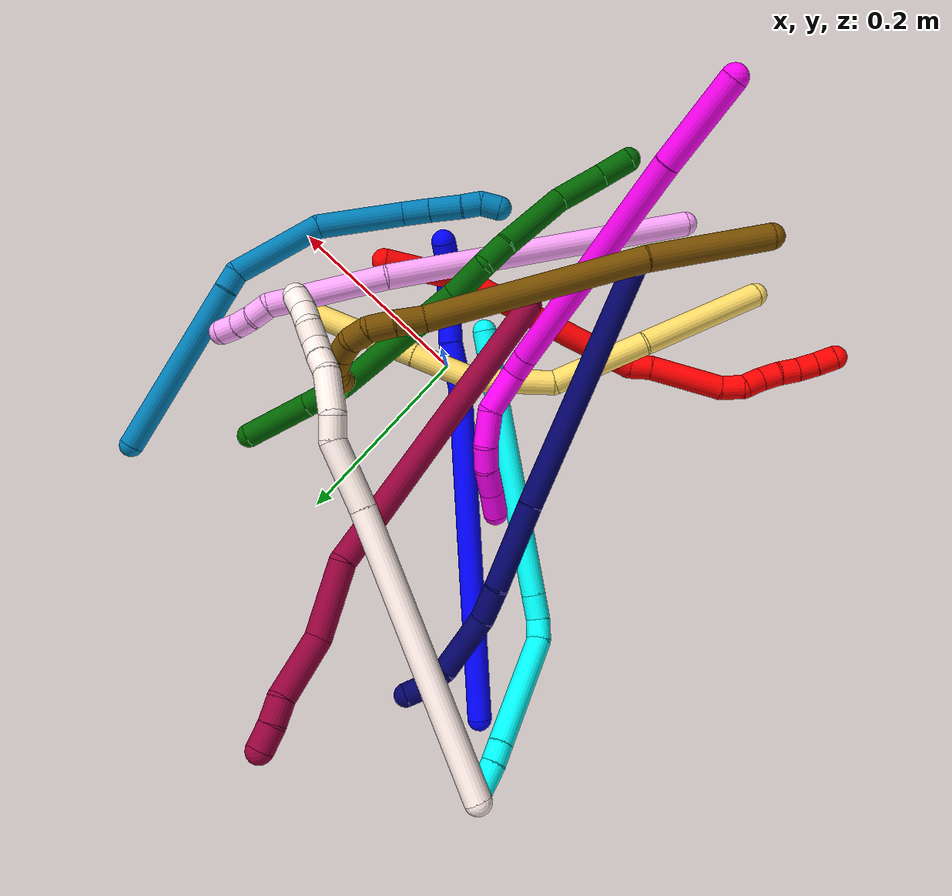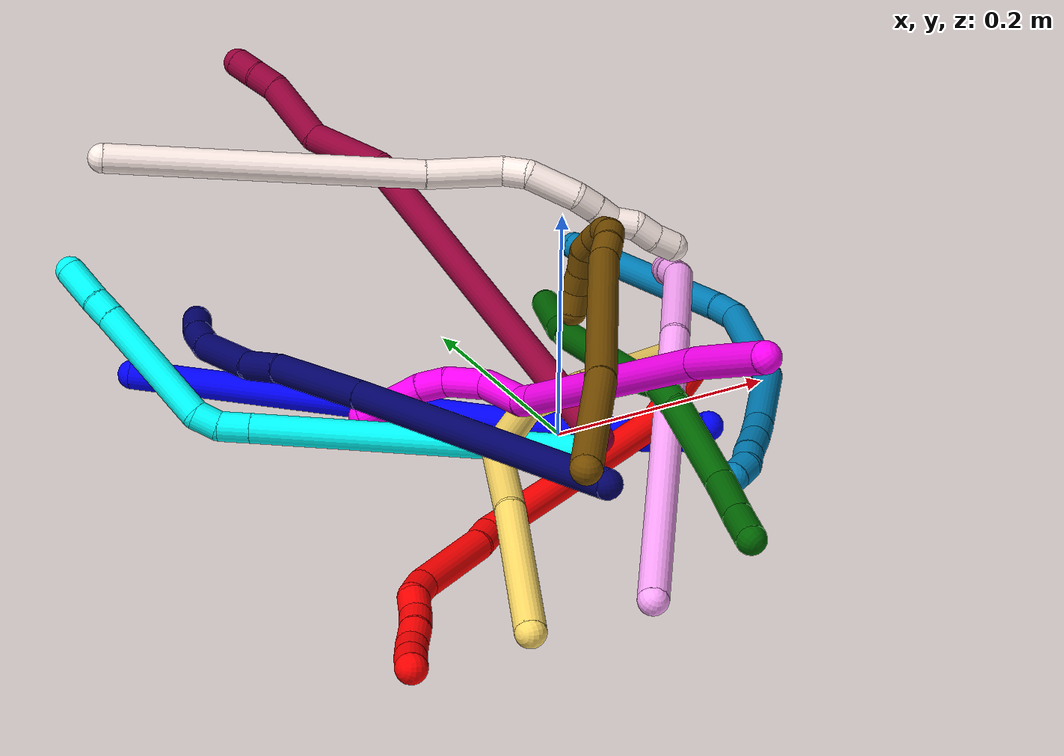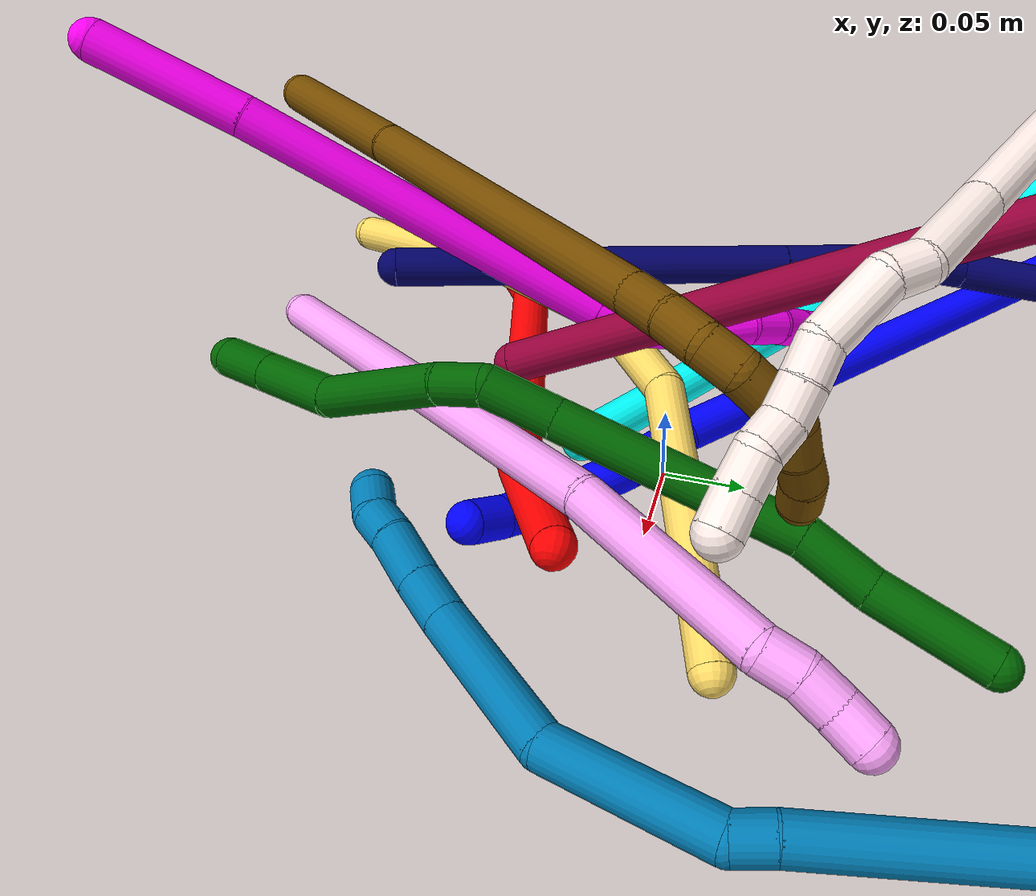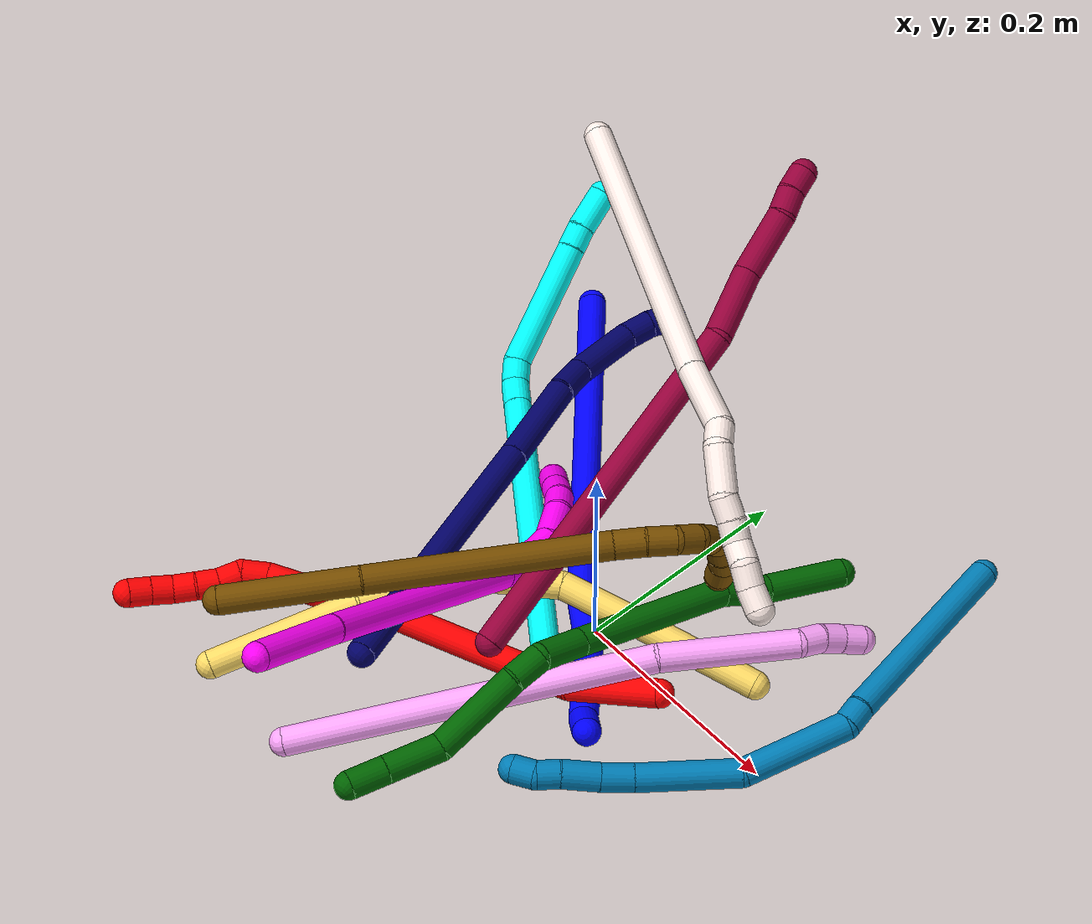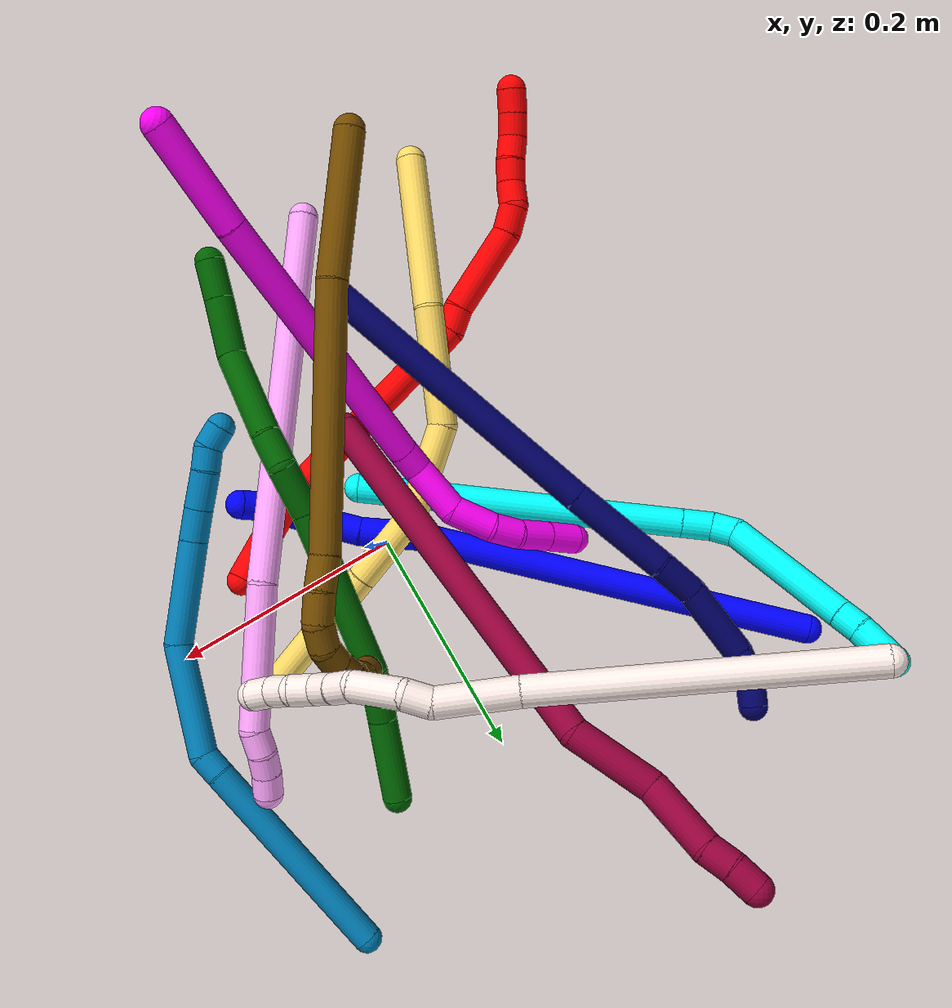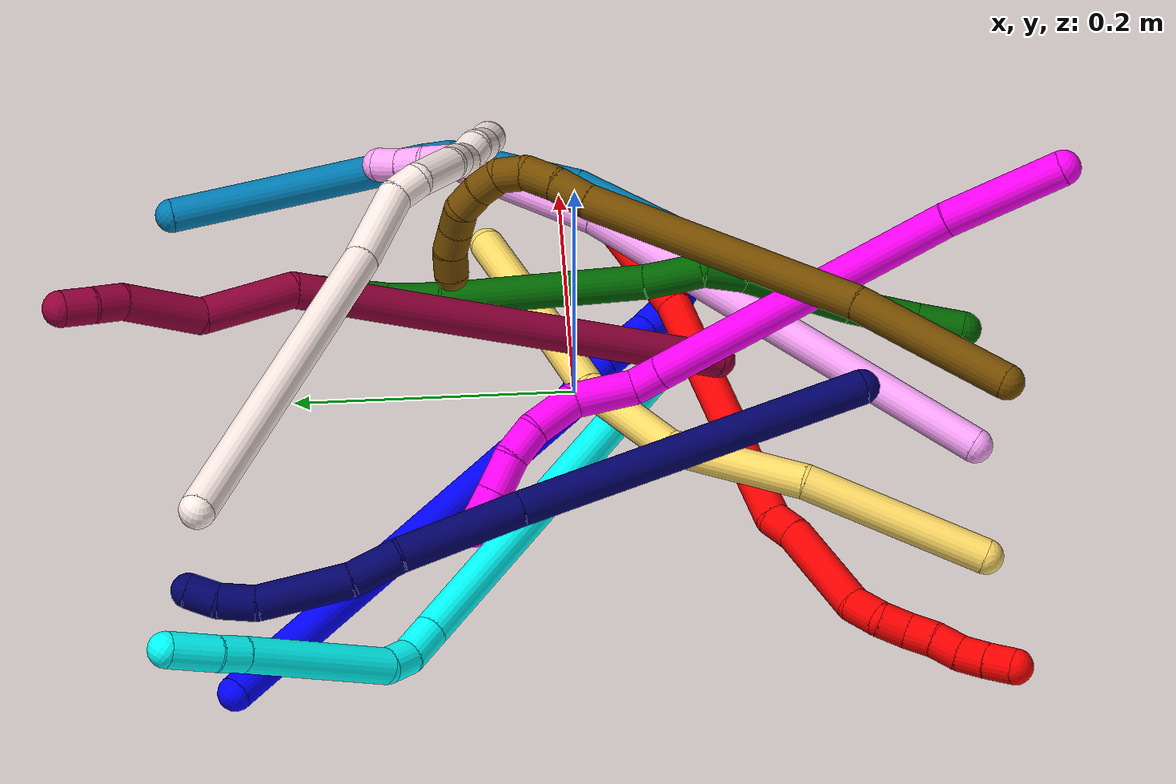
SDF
<sdf version="1.7">
 <world name="default">
  <plugin name="TubeGeneratorPlugin" filename="libtube_generator_plugin.so"/>
  <model name="photoneo_s_sensor">
   <static>1</static>
   <pose>0 0 2 1.57079 1.57079 3.14159</pose>
   <link name="link">
    <inertial><mass>0.1</mass></inertial>
    <sensor name="sensor" type="depth">
     <update_rate>30</update_rate>
     <camera>
      <horizontal_fov>1.22</horizontal_fov>
      <image><width>1920</width><height>1200</height><format>B8G8R8</format></image>
      <clip><near>0.1</near><far>4</far></clip>
      <depth_camera><output>points</output></depth_camera>
     </camera>
     <plugin name="camera_plugin" filename="libgazebo_ros_depth_camera.so">
      <baseline>0.2</baseline>
      <alwaysOn>1</alwaysOn>
      <updateRate>0.0</updateRate>
      <cameraName>camera_ir</cameraName>
      <imageTopicName>/camera/color/image_raw</imageTopicName>
      <cameraInfoTopicName>/camera/color/camera_info</cameraInfoTopicName>
      <depthImageTopicName>/camera/depth/image_raw</depthImageTopicName>
      <depthImageCameraInfoTopicName>/camera/depth/camera_info</depthImageCameraInfoTopicName>
      <pointCloudTopicName>/camera/depth/points</pointCloudTopicName>
      <frameName>fr_optical</frameName>
      <pointCloudCutoff>0.1</pointCloudCutoff>
      <pointCloudCutoffMax>2.0</pointCloudCutoffMax>
      <distortionK1>0</distortionK1>
      <distortionK2>0</distortionK2>
      <distortionK3>0</distortionK3>
      <distortionT1>0</distortionT1>
      <distortionT2>0</distortionT2>
      <CxPrime>0</CxPrime>
      <Cx>0</Cx>
      <Cy>0</Cy>
      <focalLength>0</focalLength>
      <hackBaseline>0</hackBaseline>
     </plugin>
    </sensor>
   </link>
  </model>
  <gravity>0 0 -9.8</gravity>
  <magnetic_field>6e-06 2.3e-05 -4.2e-05</magnetic_field>
  <atmosphere type="adiabatic"/>
  <physics name="default_physics" default="0" type="ode">
   <max_step_size>0.003</max_step_size>
   <real_time_factor>1</real_time_factor>
   <real_time_update_rate>1000</real_time_update_rate>
   <max_contacts>10000</max_contacts>
   <ode>
    <solver>
     <type>quick</type>
     <iters>100</iters>
     <sor>1.3</sor>
     <use_dynamic_moi_rescaling>0</use_dynamic_moi_rescaling>
    </solver>
    <constraints>
     <contact_max_correcting_vel>0</contact_max_correcting_vel>
     <contact_surface_layer>0.001</contact_surface_layer>
     <cfm>0</cfm>
     <erp>0.2</erp>
    </constraints>
   </ode>
  </physics>
  <scene><ambient>0.4 0.4 0.4 1</ambient><background>0.7 0.7 0.7 1</background><shadows>0</shadows></scene>
  <audio><device>default</device></audio>
  <spherical_coordinates>
   <surface_model>EARTH_WGS84</surface_model>
   <latitude_deg>0</latitude_deg>
   <longitude_deg>0</longitude_deg>
   <elevation>0</elevation>
   <heading_deg>0</heading_deg>
  </spherical_coordinates>
  <model name="bin">
   <static>1</static>
   <link name="bottom">
    <collision name="collision-bottom">
     <pose>0 0 -0.01 0 -0 0</pose>
     <geometry><box><size>0.8 0.6 0.02</size></box></geometry>
     <surface>
      <friction><ode><mu>100</mu><mu2>100</mu2></ode></friction>
      <contact><collide_bitmask>65535</collide_bitmask></contact>
     </surface>
    </collision>
   </link>
   <link name="west_wall">
    <collision name="collision-west_wall">
     <pose>-0.41 0 0.1 0 -0 0</pose>
     <geometry><box><size>0.02 0.6 0.2</size></box></geometry>
     <surface>
      <friction><ode><mu>100</mu><mu2>100</mu2></ode></friction>
      <contact><collide_bitmask>65535</collide_bitmask></contact>
     </surface>
    </collision>
   </link>
   <link name="east_wall">
    <collision name="collision-east_wall">
     <pose>0.41 0 0.1 0 -0 0</pose>
     <geometry><box><size>0.02 0.6 0.2</size></box></geometry>
     <surface>
      <friction><ode><mu>100</mu><mu2>100</mu2></ode></friction>
      <contact><collide_bitmask>65535</collide_bitmask></contact>
     </surface>
    </collision>
   </link>
   <link name="south_wall">
    <collision name="collision-south_wall">
     <pose>0 -0.31 0.1 0 -0 0</pose>
     <geometry><box><size>0.8 0.02 0.2</size></box></geometry>
     <surface>
      <friction><ode><mu>100</mu><mu2>100</mu2></ode></friction>
      <contact><collide_bitmask>65535</collide_bitmask></contact>
     </surface>
    </collision>
   </link>
   <link name="north_wall">
    <collision name="collision-north_wall">
     <pose>0 0.31 0.1 0 -0 0</pose>
     <geometry><box><size>0.8 0.02 0.2</size></box></geometry>
     <surface>
      <friction><ode><mu>100</mu><mu2>100</mu2></ode></friction>
      <contact><collide_bitmask>65535</collide_bitmask></contact>
     </surface>
    </collision>
   </link>
  </model>
  <model name="1">
   <static>0</static>
   <link name="1">
    <collision name="collision-cylinder-e_1_1_4">
     <pose>0.086102 -0.117938 -0.092209 2.23437 0.521937 1.00229</pose>
     <geometry><cylinder><radius>0.0125</radius><length>0.345401</length></cylinder></geometry>
     <surface>
      <friction><ode><mu>1.16</mu><mu2>1.16</mu2><slip1>0</slip1><slip2>0</slip2></ode></friction>
      <contact><ode><kp>1e+06</kp><kd>1</kd><max_vel>0</max_vel><min_depth>0.001</min_depth></ode></contact>
     </surface>
    </collision>
    <visual name="visual-cylinder-e_1_1_4">
     <pose>0.086102 -0.117938 -0.092209 2.23437 0.521937 1.00229</pose>
     <geometry><cylinder><radius>0.0125</radius><length>0.345401</length></cylinder></geometry>
     <material><ambient>0 0 1 1</ambient></material>
    </visual>
    <collision name="collision-cylinder-e_2_4_5">
     <pose>0.181406 -0.25455 -0.196151 2.13176 0.395308 0.695258</pose>
     <geometry><cylinder><radius>0.0125</radius><length>0.047793</length></cylinder></geometry>
     <surface>
      <friction><ode><mu>1.16</mu><mu2>1.16</mu2><slip1>0</slip1><slip2>0</slip2></ode></friction>
      <contact><ode><kp>1e+06</kp><kd>1</kd><max_vel>0</max_vel><min_depth>0.001</min_depth></ode></contact>
     </surface>
    </collision>
    <visual name="visual-cylinder-e_2_4_5">
     <pose>0.181406 -0.25455 -0.196151 2.13176 0.395308 0.695258</pose>
     <geometry><cylinder><radius>0.0125</radius><length>0.047793</length></cylinder></geometry>
     <material><ambient>0 0 1 1</ambient></material>
    </visual>
    <collision name="collision-cylinder-e_3_5_6">
     <pose>0.203257 -0.28963 -0.220605 2.23038 0.547227 1.04032</pose>
     <geometry><cylinder><radius>0.0125</radius><length>0.048622</length></cylinder></geometry>
     <surface>
      <friction><ode><mu>1.16</mu><mu2>1.16</mu2><slip1>0</slip1><slip2>0</slip2></ode></friction>
      <contact><ode><kp>1e+06</kp><kd>1</kd><max_vel>0</max_vel><min_depth>0.001</min_depth></ode></contact>
     </surface>
    </collision>
    <visual name="visual-cylinder-e_3_5_6">
     <pose>0.203257 -0.28963 -0.220605 2.23038 0.547227 1.04032</pose>
     <geometry><cylinder><radius>0.0125</radius><length>0.048622</length></cylinder></geometry>
     <material><ambient>0 0 1 1</ambient></material>
    </visual>
    <collision name="collision-cylinder-e_4_6_7">
     <pose>0.223354 -0.316211 -0.244395 2.39819 0.459919 1.08163</pose>
     <geometry><cylinder><radius>0.0125</radius><length>0.033555</length></cylinder></geometry>
     <surface>
      <friction><ode><mu>1.16</mu><mu2>1.16</mu2><slip1>0</slip1><slip2>0</slip2></ode></friction>
      <contact><ode><kp>1e+06</kp><kd>1</kd><max_vel>0</max_vel><min_depth>0.001</min_depth></ode></contact>
     </surface>
    </collision>
    <visual name="visual-cylinder-e_4_6_7">
     <pose>0.223354 -0.316211 -0.244395 2.39819 0.459919 1.08163</pose>
     <geometry><cylinder><radius>0.0125</radius><length>0.033555</length></cylinder></geometry>
     <material><ambient>0 0 1 1</ambient></material>
    </visual>
    <collision name="collision-cylinder-e_5_7_2">
     <pose>0.231977 -0.33355 -0.26541 2.51742 0.095603 0.294406</pose>
     <geometry><cylinder><radius>0.0125</radius><length>0.02463</length></cylinder></geometry>
     <surface>
      <friction><ode><mu>1.16</mu><mu2>1.16</mu2><slip1>0</slip1><slip2>0</slip2></ode></friction>
      <contact><ode><kp>1e+06</kp><kd>1</kd><max_vel>0</max_vel><min_depth>0.001</min_depth></ode></contact>
     </surface>
    </collision>
    <visual name="visual-cylinder-e_5_7_2">
     <pose>0.231977 -0.33355 -0.26541 2.51742 0.095603 0.294406</pose>
     <geometry><cylinder><radius>0.0125</radius><length>0.02463</length></cylinder></geometry>
     <material><ambient>0 0 1 1</ambient></material>
    </visual>
    <collision name="collision-sphere-2">
     <pose>0.233152 -0.340714 -0.275357 0 -0 0</pose>
     <geometry><sphere><radius>0.0125</radius></sphere></geometry>
     <surface>
      <friction><ode><mu>1.16</mu><mu2>1.16</mu2><slip1>0</slip1><slip2>0</slip2></ode></friction>
      <contact><ode><kp>1e+06</kp><kd>1</kd><max_vel>0</max_vel><min_depth>0.001</min_depth></ode></contact>
     </surface>
    </collision>
    <visual name="visual-sphere-2">
     <pose>0.233152 -0.340714 -0.275357 0 -0 0</pose>
     <geometry><sphere><radius>0.0125</radius></sphere></geometry>
     <material><ambient>0 0 1 1</ambient></material>
    </visual>
    <collision name="collision-sphere-7">
     <pose>0.230801 -0.326386 -0.255462 0 -0 0</pose>
     <geometry><sphere><radius>0.0125</radius></sphere></geometry>
     <surface>
      <friction><ode><mu>1.16</mu><mu2>1.16</mu2><slip1>0</slip1><slip2>0</slip2></ode></friction>
      <contact><ode><kp>1e+06</kp><kd>1</kd><max_vel>0</max_vel><min_depth>0.001</min_depth></ode></contact>
     </surface>
    </collision>
    <visual name="visual-sphere-7">
     <pose>0.230801 -0.326386 -0.255462 0 -0 0</pose>
     <geometry><sphere><radius>0.0125</radius></sphere></geometry>
     <material><ambient>0 0 1 1</ambient></material>
    </visual>
    <collision name="collision-sphere-6">
     <pose>0.215907 -0.306036 -0.233327 0 -0 0</pose>
     <geometry><sphere><radius>0.0125</radius></sphere></geometry>
     <surface>
      <friction><ode><mu>1.16</mu><mu2>1.16</mu2><slip1>0</slip1><slip2>0</slip2></ode></friction>
      <contact><ode><kp>1e+06</kp><kd>1</kd><max_vel>0</max_vel><min_depth>0.001</min_depth></ode></contact>
     </surface>
    </collision>
    <visual name="visual-sphere-6">
     <pose>0.215907 -0.306036 -0.233327 0 -0 0</pose>
     <geometry><sphere><radius>0.0125</radius></sphere></geometry>
     <material><ambient>0 0 1 1</ambient></material>
    </visual>
    <collision name="collision-sphere-5">
     <pose>0.190608 -0.273224 -0.207883 0 -0 0</pose>
     <geometry><sphere><radius>0.0125</radius></sphere></geometry>
     <surface>
      <friction><ode><mu>1.16</mu><mu2>1.16</mu2><slip1>0</slip1><slip2>0</slip2></ode></friction>
      <contact><ode><kp>1e+06</kp><kd>1</kd><max_vel>0</max_vel><min_depth>0.001</min_depth></ode></contact>
     </surface>
    </collision>
    <visual name="visual-sphere-5">
     <pose>0.190608 -0.273224 -0.207883 0 -0 0</pose>
     <geometry><sphere><radius>0.0125</radius></sphere></geometry>
     <material><ambient>0 0 1 1</ambient></material>
    </visual>
    <collision name="collision-sphere-1">
     <geometry><sphere><radius>0.0125</radius></sphere></geometry>
     <surface>
      <friction><ode><mu>1.16</mu><mu2>1.16</mu2><slip1>0</slip1><slip2>0</slip2></ode></friction>
      <contact><ode><kp>1e+06</kp><kd>1</kd><max_vel>0</max_vel><min_depth>0.001</min_depth></ode></contact>
     </surface>
    </collision>
    <visual name="visual-sphere-1">
     <geometry><sphere><radius>0.0125</radius></sphere></geometry>
     <material><ambient>0 0 1 1</ambient></material>
    </visual>
    <collision name="collision-sphere-4">
     <pose>0.172203 -0.235876 -0.184418 0 -0 0</pose>
     <geometry><sphere><radius>0.0125</radius></sphere></geometry>
     <surface>
      <friction><ode><mu>1.16</mu><mu2>1.16</mu2><slip1>0</slip1><slip2>0</slip2></ode></friction>
      <contact><ode><kp>1e+06</kp><kd>1</kd><max_vel>0</max_vel><min_depth>0.001</min_depth></ode></contact>
     </surface>
    </collision>
    <visual name="visual-sphere-4">
     <pose>0.172203 -0.235876 -0.184418 0 -0 0</pose>
     <geometry><sphere><radius>0.0125</radius></sphere></geometry>
     <material><ambient>0 0 1 1</ambient></material>
    </visual>
    <inertial>
     <pose>0.123001 -0.171619 -0.133375 0 -0 0</pose>
     <mass>0.5</mass>
     <inertia>
      <ixx>0.004181</ixx>
      <ixy>0</ixy>
      <ixz>0</ixz>
      <iyy>0.002505</iyy>
      <iyz>0</iyz>
      <izz>0.000622</izz>
     </inertia>
    </inertial>
   </link>
   <pose>-0.276782 0.245338 0.012512 2.85285 0.567874 -1.69768</pose>
  </model>
  <model name="2">
   <static>0</static>
   <link name="2">
    <collision name="collision-cylinder-e_1_1_4">
     <pose>-0.026386 0.002567 0.030684 -0.083461 -0.708506 0.030884</pose>
     <geometry><cylinder><radius>0.0125</radius><length>0.081099</length></cylinder></geometry>
     <surface>
      <friction><ode><mu>1.16</mu><mu2>1.16</mu2><slip1>0</slip1><slip2>0</slip2></ode></friction>
      <contact><ode><kp>1e+06</kp><kd>1</kd><max_vel>0</max_vel><min_depth>0.001</min_depth></ode></contact>
     </surface>
    </collision>
    <visual name="visual-cylinder-e_1_1_4">
     <pose>-0.026386 0.002567 0.030684 -0.083461 -0.708506 0.030884</pose>
     <geometry><cylinder><radius>0.0125</radius><length>0.081099</length></cylinder></geometry>
     <material><ambient>1 0 0 1</ambient></material>
    </visual>
    <collision name="collision-cylinder-e_2_4_5">
     <pose>-0.094091 0.0217 0.14938 -0.186047 -0.432267 0.040962</pose>
     <geometry><cylinder><radius>0.0125</radius><length>0.197261</length></cylinder></geometry>
     <surface>
      <friction><ode><mu>1.16</mu><mu2>1.16</mu2><slip1>0</slip1><slip2>0</slip2></ode></friction>
      <contact><ode><kp>1e+06</kp><kd>1</kd><max_vel>0</max_vel><min_depth>0.001</min_depth></ode></contact>
     </surface>
    </collision>
    <visual name="visual-cylinder-e_2_4_5">
     <pose>-0.094091 0.0217 0.14938 -0.186047 -0.432267 0.040962</pose>
     <geometry><cylinder><radius>0.0125</radius><length>0.197261</length></cylinder></geometry>
     <material><ambient>1 0 0 1</ambient></material>
    </visual>
    <collision name="collision-cylinder-e_3_5_6">
     <pose>-0.141356 0.035654 0.246101 0.29137 -0.579216 -0.087388</pose>
     <geometry><cylinder><radius>0.0125</radius><length>0.021726</length></cylinder></geometry>
     <surface>
      <friction><ode><mu>1.16</mu><mu2>1.16</mu2><slip1>0</slip1><slip2>0</slip2></ode></friction>
      <contact><ode><kp>1e+06</kp><kd>1</kd><max_vel>0</max_vel><min_depth>0.001</min_depth></ode></contact>
     </surface>
    </collision>
    <visual name="visual-cylinder-e_3_5_6">
     <pose>-0.141356 0.035654 0.246101 0.29137 -0.579216 -0.087388</pose>
     <geometry><cylinder><radius>0.0125</radius><length>0.021726</length></cylinder></geometry>
     <material><ambient>1 0 0 1</ambient></material>
    </visual>
    <collision name="collision-cylinder-e_4_6_7">
     <pose>-0.164246 0.030833 0.28858 0.065351 -0.464169 -0.01545</pose>
     <geometry><cylinder><radius>0.0125</radius><length>0.075695</length></cylinder></geometry>
     <surface>
      <friction><ode><mu>1.16</mu><mu2>1.16</mu2><slip1>0</slip1><slip2>0</slip2></ode></friction>
      <contact><ode><kp>1e+06</kp><kd>1</kd><max_vel>0</max_vel><min_depth>0.001</min_depth></ode></contact>
     </surface>
    </collision>
    <visual name="visual-cylinder-e_4_6_7">
     <pose>-0.164246 0.030833 0.28858 0.065351 -0.464169 -0.01545</pose>
     <geometry><cylinder><radius>0.0125</radius><length>0.075695</length></cylinder></geometry>
     <material><ambient>1 0 0 1</ambient></material>
    </visual>
    <collision name="collision-cylinder-e_5_7_8">
     <pose>-0.18769 0.024674 0.331346 0.413641 -0.584571 -0.126104</pose>
     <geometry><cylinder><radius>0.0125</radius><length>0.023559</length></cylinder></geometry>
     <surface>
      <friction><ode><mu>1.16</mu><mu2>1.16</mu2><slip1>0</slip1><slip2>0</slip2></ode></friction>
      <contact><ode><kp>1e+06</kp><kd>1</kd><max_vel>0</max_vel><min_depth>0.001</min_depth></ode></contact>
     </surface>
    </collision>
    <visual name="visual-cylinder-e_5_7_8">
     <pose>-0.18769 0.024674 0.331346 0.413641 -0.584571 -0.126104</pose>
     <geometry><cylinder><radius>0.0125</radius><length>0.023559</length></cylinder></geometry>
     <material><ambient>1 0 0 1</ambient></material>
    </visual>
    <collision name="collision-cylinder-e_6_8_9">
     <pose>-0.203056 0.017227 0.344287 0.725324 -1.0341 -0.425028</pose>
     <geometry><cylinder><radius>0.0125</radius><length>0.020632</length></cylinder></geometry>
     <surface>
      <friction><ode><mu>1.16</mu><mu2>1.16</mu2><slip1>0</slip1><slip2>0</slip2></ode></friction>
      <contact><ode><kp>1e+06</kp><kd>1</kd><max_vel>0</max_vel><min_depth>0.001</min_depth></ode></contact>
     </surface>
    </collision>
    <visual name="visual-cylinder-e_6_8_9">
     <pose>-0.203056 0.017227 0.344287 0.725324 -1.0341 -0.425028</pose>
     <geometry><cylinder><radius>0.0125</radius><length>0.020632</length></cylinder></geometry>
     <material><ambient>1 0 0 1</ambient></material>
    </visual>
    <collision name="collision-cylinder-e_7_9_10">
     <pose>-0.218926 0.009168 0.353744 0.691304 -0.774996 -0.291855</pose>
     <geometry><cylinder><radius>0.0125</radius><length>0.020022</length></cylinder></geometry>
     <surface>
      <friction><ode><mu>1.16</mu><mu2>1.16</mu2><slip1>0</slip1><slip2>0</slip2></ode></friction>
      <contact><ode><kp>1e+06</kp><kd>1</kd><max_vel>0</max_vel><min_depth>0.001</min_depth></ode></contact>
     </surface>
    </collision>
    <visual name="visual-cylinder-e_7_9_10">
     <pose>-0.218926 0.009168 0.353744 0.691304 -0.774996 -0.291855</pose>
     <geometry><cylinder><radius>0.0125</radius><length>0.020022</length></cylinder></geometry>
     <material><ambient>1 0 0 1</ambient></material>
    </visual>
    <collision name="collision-cylinder-e_8_10_11">
     <pose>-0.233381 0.001555 0.365188 0.475139 -0.840381 -0.21554</pose>
     <geometry><cylinder><radius>0.0125</radius><length>0.020003</length></cylinder></geometry>
     <surface>
      <friction><ode><mu>1.16</mu><mu2>1.16</mu2><slip1>0</slip1><slip2>0</slip2></ode></friction>
      <contact><ode><kp>1e+06</kp><kd>1</kd><max_vel>0</max_vel><min_depth>0.001</min_depth></ode></contact>
     </surface>
    </collision>
    <visual name="visual-cylinder-e_8_10_11">
     <pose>-0.233381 0.001555 0.365188 0.475139 -0.840381 -0.21554</pose>
     <geometry><cylinder><radius>0.0125</radius><length>0.020003</length></cylinder></geometry>
     <material><ambient>1 0 0 1</ambient></material>
    </visual>
    <collision name="collision-cylinder-e_9_11_12">
     <pose>-0.247023 -0.00666 0.377039 0.717364 -0.667672 -0.258592</pose>
     <geometry><cylinder><radius>0.0125</radius><length>0.020001</length></cylinder></geometry>
     <surface>
      <friction><ode><mu>1.16</mu><mu2>1.16</mu2><slip1>0</slip1><slip2>0</slip2></ode></friction>
      <contact><ode><kp>1e+06</kp><kd>1</kd><max_vel>0</max_vel><min_depth>0.001</min_depth></ode></contact>
     </surface>
    </collision>
    <visual name="visual-cylinder-e_9_11_12">
     <pose>-0.247023 -0.00666 0.377039 0.717364 -0.667672 -0.258592</pose>
     <geometry><cylinder><radius>0.0125</radius><length>0.020001</length></cylinder></geometry>
     <material><ambient>1 0 0 1</ambient></material>
    </visual>
    <collision name="collision-cylinder-e_10_12_2">
     <pose>-0.259456 -0.017432 0.388398 0.80069 -0.673875 -0.294346</pose>
     <geometry><cylinder><radius>0.0125</radius><length>0.020001</length></cylinder></geometry>
     <surface>
      <friction><ode><mu>1.16</mu><mu2>1.16</mu2><slip1>0</slip1><slip2>0</slip2></ode></friction>
      <contact><ode><kp>1e+06</kp><kd>1</kd><max_vel>0</max_vel><min_depth>0.001</min_depth></ode></contact>
     </surface>
    </collision>
    <visual name="visual-cylinder-e_10_12_2">
     <pose>-0.259456 -0.017432 0.388398 0.80069 -0.673875 -0.294346</pose>
     <geometry><cylinder><radius>0.0125</radius><length>0.020001</length></cylinder></geometry>
     <material><ambient>1 0 0 1</ambient></material>
    </visual>
    <collision name="collision-sphere-2">
     <pose>-0.265696 -0.023042 0.393838 0 -0 0</pose>
     <geometry><sphere><radius>0.0125</radius></sphere></geometry>
     <surface>
      <friction><ode><mu>1.16</mu><mu2>1.16</mu2><slip1>0</slip1><slip2>0</slip2></ode></friction>
      <contact><ode><kp>1e+06</kp><kd>1</kd><max_vel>0</max_vel><min_depth>0.001</min_depth></ode></contact>
     </surface>
    </collision>
    <visual name="visual-sphere-2">
     <pose>-0.265696 -0.023042 0.393838 0 -0 0</pose>
     <geometry><sphere><radius>0.0125</radius></sphere></geometry>
     <material><ambient>1 0 0 1</ambient></material>
    </visual>
    <collision name="collision-sphere-12">
     <pose>-0.253215 -0.011822 0.382957 0 -0 0</pose>
     <geometry><sphere><radius>0.0125</radius></sphere></geometry>
     <surface>
      <friction><ode><mu>1.16</mu><mu2>1.16</mu2><slip1>0</slip1><slip2>0</slip2></ode></friction>
      <contact><ode><kp>1e+06</kp><kd>1</kd><max_vel>0</max_vel><min_depth>0.001</min_depth></ode></contact>
     </surface>
    </collision>
    <visual name="visual-sphere-12">
     <pose>-0.253215 -0.011822 0.382957 0 -0 0</pose>
     <geometry><sphere><radius>0.0125</radius></sphere></geometry>
     <material><ambient>1 0 0 1</ambient></material>
    </visual>
    <collision name="collision-sphere-11">
     <pose>-0.240831 -0.001497 0.371122 0 -0 0</pose>
     <geometry><sphere><radius>0.0125</radius></sphere></geometry>
     <surface>
      <friction><ode><mu>1.16</mu><mu2>1.16</mu2><slip1>0</slip1><slip2>0</slip2></ode></friction>
      <contact><ode><kp>1e+06</kp><kd>1</kd><max_vel>0</max_vel><min_depth>0.001</min_depth></ode></contact>
     </surface>
    </collision>
    <visual name="visual-sphere-11">
     <pose>-0.240831 -0.001497 0.371122 0 -0 0</pose>
     <geometry><sphere><radius>0.0125</radius></sphere></geometry>
     <material><ambient>1 0 0 1</ambient></material>
    </visual>
    <collision name="collision-sphere-10">
     <pose>-0.225931 0.004608 0.359255 0 -0 0</pose>
     <geometry><sphere><radius>0.0125</radius></sphere></geometry>
     <surface>
      <friction><ode><mu>1.16</mu><mu2>1.16</mu2><slip1>0</slip1><slip2>0</slip2></ode></friction>
      <contact><ode><kp>1e+06</kp><kd>1</kd><max_vel>0</max_vel><min_depth>0.001</min_depth></ode></contact>
     </surface>
    </collision>
    <visual name="visual-sphere-10">
     <pose>-0.225931 0.004608 0.359255 0 -0 0</pose>
     <geometry><sphere><radius>0.0125</radius></sphere></geometry>
     <material><ambient>1 0 0 1</ambient></material>
    </visual>
    <collision name="collision-sphere-9">
     <pose>-0.211921 0.013727 0.348234 0 -0 0</pose>
     <geometry><sphere><radius>0.0125</radius></sphere></geometry>
     <surface>
      <friction><ode><mu>1.16</mu><mu2>1.16</mu2><slip1>0</slip1><slip2>0</slip2></ode></friction>
      <contact><ode><kp>1e+06</kp><kd>1</kd><max_vel>0</max_vel><min_depth>0.001</min_depth></ode></contact>
     </surface>
    </collision>
    <visual name="visual-sphere-9">
     <pose>-0.211921 0.013727 0.348234 0 -0 0</pose>
     <geometry><sphere><radius>0.0125</radius></sphere></geometry>
     <material><ambient>1 0 0 1</ambient></material>
    </visual>
    <collision name="collision-sphere-4">
     <pose>-0.052771 0.005134 0.061367 0 -0 0</pose>
     <geometry><sphere><radius>0.0125</radius></sphere></geometry>
     <surface>
      <friction><ode><mu>1.16</mu><mu2>1.16</mu2><slip1>0</slip1><slip2>0</slip2></ode></friction>
      <contact><ode><kp>1e+06</kp><kd>1</kd><max_vel>0</max_vel><min_depth>0.001</min_depth></ode></contact>
     </surface>
    </collision>
    <visual name="visual-sphere-4">
     <pose>-0.052771 0.005134 0.061367 0 -0 0</pose>
     <geometry><sphere><radius>0.0125</radius></sphere></geometry>
     <material><ambient>1 0 0 1</ambient></material>
    </visual>
    <collision name="collision-sphere-1">
     <geometry><sphere><radius>0.0125</radius></sphere></geometry>
     <surface>
      <friction><ode><mu>1.16</mu><mu2>1.16</mu2><slip1>0</slip1><slip2>0</slip2></ode></friction>
      <contact><ode><kp>1e+06</kp><kd>1</kd><max_vel>0</max_vel><min_depth>0.001</min_depth></ode></contact>
     </surface>
    </collision>
    <visual name="visual-sphere-1">
     <geometry><sphere><radius>0.0125</radius></sphere></geometry>
     <material><ambient>1 0 0 1</ambient></material>
    </visual>
    <collision name="collision-sphere-8">
     <pose>-0.19419 0.020726 0.340341 0 -0 0</pose>
     <geometry><sphere><radius>0.0125</radius></sphere></geometry>
     <surface>
      <friction><ode><mu>1.16</mu><mu2>1.16</mu2><slip1>0</slip1><slip2>0</slip2></ode></friction>
      <contact><ode><kp>1e+06</kp><kd>1</kd><max_vel>0</max_vel><min_depth>0.001</min_depth></ode></contact>
     </surface>
    </collision>
    <visual name="visual-sphere-8">
     <pose>-0.19419 0.020726 0.340341 0 -0 0</pose>
     <geometry><sphere><radius>0.0125</radius></sphere></geometry>
     <material><ambient>1 0 0 1</ambient></material>
    </visual>
    <collision name="collision-sphere-5">
     <pose>-0.13541 0.038266 0.237393 0 -0 0</pose>
     <geometry><sphere><radius>0.0125</radius></sphere></geometry>
     <surface>
      <friction><ode><mu>1.16</mu><mu2>1.16</mu2><slip1>0</slip1><slip2>0</slip2></ode></friction>
      <contact><ode><kp>1e+06</kp><kd>1</kd><max_vel>0</max_vel><min_depth>0.001</min_depth></ode></contact>
     </surface>
    </collision>
    <visual name="visual-sphere-5">
     <pose>-0.13541 0.038266 0.237393 0 -0 0</pose>
     <geometry><sphere><radius>0.0125</radius></sphere></geometry>
     <material><ambient>1 0 0 1</ambient></material>
    </visual>
    <collision name="collision-sphere-6">
     <pose>-0.147302 0.033043 0.254809 0 -0 0</pose>
     <geometry><sphere><radius>0.0125</radius></sphere></geometry>
     <surface>
      <friction><ode><mu>1.16</mu><mu2>1.16</mu2><slip1>0</slip1><slip2>0</slip2></ode></friction>
      <contact><ode><kp>1e+06</kp><kd>1</kd><max_vel>0</max_vel><min_depth>0.001</min_depth></ode></contact>
     </surface>
    </collision>
    <visual name="visual-sphere-6">
     <pose>-0.147302 0.033043 0.254809 0 -0 0</pose>
     <geometry><sphere><radius>0.0125</radius></sphere></geometry>
     <material><ambient>1 0 0 1</ambient></material>
    </visual>
    <collision name="collision-sphere-7">
     <pose>-0.181189 0.028623 0.322351 0 -0 0</pose>
     <geometry><sphere><radius>0.0125</radius></sphere></geometry>
     <surface>
      <friction><ode><mu>1.16</mu><mu2>1.16</mu2><slip1>0</slip1><slip2>0</slip2></ode></friction>
      <contact><ode><kp>1e+06</kp><kd>1</kd><max_vel>0</max_vel><min_depth>0.001</min_depth></ode></contact>
     </surface>
    </collision>
    <visual name="visual-sphere-7">
     <pose>-0.181189 0.028623 0.322351 0 -0 0</pose>
     <geometry><sphere><radius>0.0125</radius></sphere></geometry>
     <material><ambient>1 0 0 1</ambient></material>
    </visual>
    <inertial>
     <pose>-0.127994 0.016533 0.207506 0 -0 0</pose>
     <mass>0.5</mass>
     <inertia>
      <ixx>0.000668</ixx>
      <ixy>0</ixy>
      <ixz>0</ixz>
      <iyy>0.000755</iyy>
      <iyz>0</iyz>
      <izz>0.000253</izz>
     </inertia>
    </inertial>
   </link>
   <pose>0.114865 -0.032076 0.054781 -1.16945 -0.700282 1.3952</pose>
  </model>
  <model name="3">
   <static>0</static>
   <link name="3">
    <collision name="collision-cylinder-e_1_1_4">
     <pose>-0.057782 0.045747 0.118229 -0.369194 -0.427665 0.08105</pose>
     <geometry><cylinder><radius>0.0125</radius><length>0.278638</length></cylinder></geometry>
     <surface>
      <friction><ode><mu>1.16</mu><mu2>1.16</mu2><slip1>0</slip1><slip2>0</slip2></ode></friction>
      <contact><ode><kp>1e+06</kp><kd>1</kd><max_vel>0</max_vel><min_depth>0.001</min_depth></ode></contact>
     </surface>
    </collision>
    <visual name="visual-cylinder-e_1_1_4">
     <pose>-0.057782 0.045747 0.118229 -0.369194 -0.427665 0.08105</pose>
     <geometry><cylinder><radius>0.0125</radius><length>0.278638</length></cylinder></geometry>
     <material><ambient>0.003922 1 0.996078 1</ambient></material>
    </visual>
    <collision name="collision-cylinder-e_2_4_5">
     <pose>-0.121073 0.095861 0.247918 -0.364016 -0.422169 0.078832</pose>
     <geometry><cylinder><radius>0.0125</radius><length>0.026887</length></cylinder></geometry>
     <surface>
      <friction><ode><mu>1.16</mu><mu2>1.16</mu2><slip1>0</slip1><slip2>0</slip2></ode></friction>
      <contact><ode><kp>1e+06</kp><kd>1</kd><max_vel>0</max_vel><min_depth>0.001</min_depth></ode></contact>
     </surface>
    </collision>
    <visual name="visual-cylinder-e_2_4_5">
     <pose>-0.121073 0.095861 0.247918 -0.364016 -0.422169 0.078832</pose>
     <geometry><cylinder><radius>0.0125</radius><length>0.026887</length></cylinder></geometry>
     <material><ambient>0.003922 1 0.996078 1</ambient></material>
    </visual>
    <collision name="collision-cylinder-e_3_5_6">
     <pose>-0.134486 0.103254 0.266237 -0.415676 -0.811883 0.180787</pose>
     <geometry><cylinder><radius>0.0125</radius><length>0.021789</length></cylinder></geometry>
     <surface>
      <friction><ode><mu>1.16</mu><mu2>1.16</mu2><slip1>0</slip1><slip2>0</slip2></ode></friction>
      <contact><ode><kp>1e+06</kp><kd>1</kd><max_vel>0</max_vel><min_depth>0.001</min_depth></ode></contact>
     </surface>
    </collision>
    <visual name="visual-cylinder-e_3_5_6">
     <pose>-0.134486 0.103254 0.266237 -0.415676 -0.811883 0.180787</pose>
     <geometry><cylinder><radius>0.0125</radius><length>0.021789</length></cylinder></geometry>
     <material><ambient>0.003922 1 0.996078 1</ambient></material>
    </visual>
    <collision name="collision-cylinder-e_4_6_7">
     <pose>-0.19458 0.103962 0.296863 0.09726 -1.14165 -0.062483</pose>
     <geometry><cylinder><radius>0.0125</radius><length>0.114787</length></cylinder></geometry>
     <surface>
      <friction><ode><mu>1.16</mu><mu2>1.16</mu2><slip1>0</slip1><slip2>0</slip2></ode></friction>
      <contact><ode><kp>1e+06</kp><kd>1</kd><max_vel>0</max_vel><min_depth>0.001</min_depth></ode></contact>
     </surface>
    </collision>
    <visual name="visual-cylinder-e_4_6_7">
     <pose>-0.19458 0.103962 0.296863 0.09726 -1.14165 -0.062483</pose>
     <geometry><cylinder><radius>0.0125</radius><length>0.114787</length></cylinder></geometry>
     <material><ambient>0.003922 1 0.996078 1</ambient></material>
    </visual>
    <collision name="collision-cylinder-e_5_7_8">
     <pose>-0.256052 0.101199 0.325321 0.094422 -1.10122 -0.057997</pose>
     <geometry><cylinder><radius>0.0125</radius><length>0.02082</length></cylinder></geometry>
     <surface>
      <friction><ode><mu>1.16</mu><mu2>1.16</mu2><slip1>0</slip1><slip2>0</slip2></ode></friction>
      <contact><ode><kp>1e+06</kp><kd>1</kd><max_vel>0</max_vel><min_depth>0.001</min_depth></ode></contact>
     </surface>
    </collision>
    <visual name="visual-cylinder-e_5_7_8">
     <pose>-0.256052 0.101199 0.325321 0.094422 -1.10122 -0.057997</pose>
     <geometry><cylinder><radius>0.0125</radius><length>0.02082</length></cylinder></geometry>
     <material><ambient>0.003922 1 0.996078 1</ambient></material>
    </visual>
    <collision name="collision-cylinder-e_6_8_2">
     <pose>-0.281657 0.097873 0.338317 0.333962 -1.07668 -0.200632</pose>
     <geometry><cylinder><radius>0.0125</radius><length>0.037079</length></cylinder></geometry>
     <surface>
      <friction><ode><mu>1.16</mu><mu2>1.16</mu2><slip1>0</slip1><slip2>0</slip2></ode></friction>
      <contact><ode><kp>1e+06</kp><kd>1</kd><max_vel>0</max_vel><min_depth>0.001</min_depth></ode></contact>
     </surface>
    </collision>
    <visual name="visual-cylinder-e_6_8_2">
     <pose>-0.281657 0.097873 0.338317 0.333962 -1.07668 -0.200632</pose>
     <geometry><cylinder><radius>0.0125</radius><length>0.037079</length></cylinder></geometry>
     <material><ambient>0.003922 1 0.996078 1</ambient></material>
    </visual>
    <collision name="collision-sphere-2">
     <pose>-0.297979 0.094991 0.346624 0 -0 0</pose>
     <geometry><sphere><radius>0.0125</radius></sphere></geometry>
     <surface>
      <friction><ode><mu>1.16</mu><mu2>1.16</mu2><slip1>0</slip1><slip2>0</slip2></ode></friction>
      <contact><ode><kp>1e+06</kp><kd>1</kd><max_vel>0</max_vel><min_depth>0.001</min_depth></ode></contact>
     </surface>
    </collision>
    <visual name="visual-sphere-2">
     <pose>-0.297979 0.094991 0.346624 0 -0 0</pose>
     <geometry><sphere><radius>0.0125</radius></sphere></geometry>
     <material><ambient>0.003922 1 0.996078 1</ambient></material>
    </visual>
    <collision name="collision-sphere-4">
     <pose>-0.115564 0.091494 0.236459 0 -0 0</pose>
     <geometry><sphere><radius>0.0125</radius></sphere></geometry>
     <surface>
      <friction><ode><mu>1.16</mu><mu2>1.16</mu2><slip1>0</slip1><slip2>0</slip2></ode></friction>
      <contact><ode><kp>1e+06</kp><kd>1</kd><max_vel>0</max_vel><min_depth>0.001</min_depth></ode></contact>
     </surface>
    </collision>
    <visual name="visual-sphere-4">
     <pose>-0.115564 0.091494 0.236459 0 -0 0</pose>
     <geometry><sphere><radius>0.0125</radius></sphere></geometry>
     <material><ambient>0.003922 1 0.996078 1</ambient></material>
    </visual>
    <collision name="collision-sphere-1">
     <geometry><sphere><radius>0.0125</radius></sphere></geometry>
     <surface>
      <friction><ode><mu>1.16</mu><mu2>1.16</mu2><slip1>0</slip1><slip2>0</slip2></ode></friction>
      <contact><ode><kp>1e+06</kp><kd>1</kd><max_vel>0</max_vel><min_depth>0.001</min_depth></ode></contact>
     </surface>
    </collision>
    <visual name="visual-sphere-1">
     <geometry><sphere><radius>0.0125</radius></sphere></geometry>
     <material><ambient>0.003922 1 0.996078 1</ambient></material>
    </visual>
    <collision name="collision-sphere-8">
     <pose>-0.265335 0.100755 0.330011 0 -0 0</pose>
     <geometry><sphere><radius>0.0125</radius></sphere></geometry>
     <surface>
      <friction><ode><mu>1.16</mu><mu2>1.16</mu2><slip1>0</slip1><slip2>0</slip2></ode></friction>
      <contact><ode><kp>1e+06</kp><kd>1</kd><max_vel>0</max_vel><min_depth>0.001</min_depth></ode></contact>
     </surface>
    </collision>
    <visual name="visual-sphere-8">
     <pose>-0.265335 0.100755 0.330011 0 -0 0</pose>
     <geometry><sphere><radius>0.0125</radius></sphere></geometry>
     <material><ambient>0.003922 1 0.996078 1</ambient></material>
    </visual>
    <collision name="collision-sphere-5">
     <pose>-0.126581 0.100227 0.259378 0 -0 0</pose>
     <geometry><sphere><radius>0.0125</radius></sphere></geometry>
     <surface>
      <friction><ode><mu>1.16</mu><mu2>1.16</mu2><slip1>0</slip1><slip2>0</slip2></ode></friction>
      <contact><ode><kp>1e+06</kp><kd>1</kd><max_vel>0</max_vel><min_depth>0.001</min_depth></ode></contact>
     </surface>
    </collision>
    <visual name="visual-sphere-5">
     <pose>-0.126581 0.100227 0.259378 0 -0 0</pose>
     <geometry><sphere><radius>0.0125</radius></sphere></geometry>
     <material><ambient>0.003922 1 0.996078 1</ambient></material>
    </visual>
    <collision name="collision-sphere-6">
     <pose>-0.142391 0.106281 0.273095 0 -0 0</pose>
     <geometry><sphere><radius>0.0125</radius></sphere></geometry>
     <surface>
      <friction><ode><mu>1.16</mu><mu2>1.16</mu2><slip1>0</slip1><slip2>0</slip2></ode></friction>
      <contact><ode><kp>1e+06</kp><kd>1</kd><max_vel>0</max_vel><min_depth>0.001</min_depth></ode></contact>
     </surface>
    </collision>
    <visual name="visual-sphere-6">
     <pose>-0.142391 0.106281 0.273095 0 -0 0</pose>
     <geometry><sphere><radius>0.0125</radius></sphere></geometry>
     <material><ambient>0.003922 1 0.996078 1</ambient></material>
    </visual>
    <collision name="collision-sphere-7">
     <pose>-0.246769 0.101643 0.320632 0 -0 0</pose>
     <geometry><sphere><radius>0.0125</radius></sphere></geometry>
     <surface>
      <friction><ode><mu>1.16</mu><mu2>1.16</mu2><slip1>0</slip1><slip2>0</slip2></ode></friction>
      <contact><ode><kp>1e+06</kp><kd>1</kd><max_vel>0</max_vel><min_depth>0.001</min_depth></ode></contact>
     </surface>
    </collision>
    <visual name="visual-sphere-7">
     <pose>-0.246769 0.101643 0.320632 0 -0 0</pose>
     <geometry><sphere><radius>0.0125</radius></sphere></geometry>
     <material><ambient>0.003922 1 0.996078 1</ambient></material>
    </visual>
    <inertial>
     <pose>-0.120791 0.070487 0.197607 0 -0 0</pose>
     <mass>0.5</mass>
     <inertia>
      <ixx>0.001813</ixx>
      <ixy>0</ixy>
      <ixz>0</ixz>
      <iyy>0.001987</iyy>
      <iyz>0</iyz>
      <izz>0.000316</izz>
     </inertia>
    </inertial>
   </link>
   <pose>-0.004237 -0.05285 0.011499 2.56641 0.910862 -1.46275</pose>
  </model>
  <model name="4">
   <static>0</static>
   <link name="4">
    <collision name="collision-cylinder-e_1_1_4">
     <pose>0.085787 0.127201 -0.044851 -1.90978 0.566498 -0.78037</pose>
     <geometry><cylinder><radius>0.0125</radius><length>0.319694</length></cylinder></geometry>
     <surface>
      <friction><ode><mu>1.16</mu><mu2>1.16</mu2><slip1>0</slip1><slip2>0</slip2></ode></friction>
      <contact><ode><kp>1e+06</kp><kd>1</kd><max_vel>0</max_vel><min_depth>0.001</min_depth></ode></contact>
     </surface>
    </collision>
    <visual name="visual-cylinder-e_1_1_4">
     <pose>0.085787 0.127201 -0.044851 -1.90978 0.566498 -0.78037</pose>
     <geometry><cylinder><radius>0.0125</radius><length>0.319694</length></cylinder></geometry>
     <material><ambient>1 0.65098 0.996078 1</ambient></material>
    </visual>
    <collision name="collision-cylinder-e_2_4_5">
     <pose>0.20318 0.296148 -0.118251 -2.17064 0.558559 -0.995765</pose>
     <geometry><cylinder><radius>0.0125</radius><length>0.119277</length></cylinder></geometry>
     <surface>
      <friction><ode><mu>1.16</mu><mu2>1.16</mu2><slip1>0</slip1><slip2>0</slip2></ode></friction>
      <contact><ode><kp>1e+06</kp><kd>1</kd><max_vel>0</max_vel><min_depth>0.001</min_depth></ode></contact>
     </surface>
    </collision>
    <visual name="visual-cylinder-e_2_4_5">
     <pose>0.20318 0.296148 -0.118251 -2.17064 0.558559 -0.995765</pose>
     <geometry><cylinder><radius>0.0125</radius><length>0.119277</length></cylinder></geometry>
     <material><ambient>1 0.65098 0.996078 1</ambient></material>
    </visual>
    <collision name="collision-cylinder-e_3_5_6">
     <pose>0.236983 0.344703 -0.154495 -2.41705 0.210656 -0.544057</pose>
     <geometry><cylinder><radius>0.0125</radius><length>0.021014</length></cylinder></geometry>
     <surface>
      <friction><ode><mu>1.16</mu><mu2>1.16</mu2><slip1>0</slip1><slip2>0</slip2></ode></friction>
      <contact><ode><kp>1e+06</kp><kd>1</kd><max_vel>0</max_vel><min_depth>0.001</min_depth></ode></contact>
     </surface>
    </collision>
    <visual name="visual-cylinder-e_3_5_6">
     <pose>0.236983 0.344703 -0.154495 -2.41705 0.210656 -0.544057</pose>
     <geometry><cylinder><radius>0.0125</radius><length>0.021014</length></cylinder></geometry>
     <material><ambient>1 0.65098 0.996078 1</ambient></material>
    </visual>
    <collision name="collision-cylinder-e_4_6_7">
     <pose>0.242465 0.35627 -0.170354 -2.61412 0.334543 -1.11764</pose>
     <geometry><cylinder><radius>0.0125</radius><length>0.020008</length></cylinder></geometry>
     <surface>
      <friction><ode><mu>1.16</mu><mu2>1.16</mu2><slip1>0</slip1><slip2>0</slip2></ode></friction>
      <contact><ode><kp>1e+06</kp><kd>1</kd><max_vel>0</max_vel><min_depth>0.001</min_depth></ode></contact>
     </surface>
    </collision>
    <visual name="visual-cylinder-e_4_6_7">
     <pose>0.242465 0.35627 -0.170354 -2.61412 0.334543 -1.11764</pose>
     <geometry><cylinder><radius>0.0125</radius><length>0.020008</length></cylinder></geometry>
     <material><ambient>1 0.65098 0.996078 1</ambient></material>
    </visual>
    <collision name="collision-cylinder-e_5_7_2">
     <pose>0.250063 0.366038 -0.186025 -2.55286 0.445857 -1.28411</pose>
     <geometry><cylinder><radius>0.0125</radius><length>0.020007</length></cylinder></geometry>
     <surface>
      <friction><ode><mu>1.16</mu><mu2>1.16</mu2><slip1>0</slip1><slip2>0</slip2></ode></friction>
      <contact><ode><kp>1e+06</kp><kd>1</kd><max_vel>0</max_vel><min_depth>0.001</min_depth></ode></contact>
     </surface>
    </collision>
    <visual name="visual-cylinder-e_5_7_2">
     <pose>0.250063 0.366038 -0.186025 -2.55286 0.445857 -1.28411</pose>
     <geometry><cylinder><radius>0.0125</radius><length>0.020007</length></cylinder></geometry>
     <material><ambient>1 0.65098 0.996078 1</ambient></material>
    </visual>
    <collision name="collision-sphere-2">
     <pose>0.254377 0.37105 -0.193531 0 -0 0</pose>
     <geometry><sphere><radius>0.0125</radius></sphere></geometry>
     <surface>
      <friction><ode><mu>1.16</mu><mu2>1.16</mu2><slip1>0</slip1><slip2>0</slip2></ode></friction>
      <contact><ode><kp>1e+06</kp><kd>1</kd><max_vel>0</max_vel><min_depth>0.001</min_depth></ode></contact>
     </surface>
    </collision>
    <visual name="visual-sphere-2">
     <pose>0.254377 0.37105 -0.193531 0 -0 0</pose>
     <geometry><sphere><radius>0.0125</radius></sphere></geometry>
     <material><ambient>1 0.65098 0.996078 1</ambient></material>
    </visual>
    <collision name="collision-sphere-7">
     <pose>0.24575 0.361026 -0.178519 0 -0 0</pose>
     <geometry><sphere><radius>0.0125</radius></sphere></geometry>
     <surface>
      <friction><ode><mu>1.16</mu><mu2>1.16</mu2><slip1>0</slip1><slip2>0</slip2></ode></friction>
      <contact><ode><kp>1e+06</kp><kd>1</kd><max_vel>0</max_vel><min_depth>0.001</min_depth></ode></contact>
     </surface>
    </collision>
    <visual name="visual-sphere-7">
     <pose>0.24575 0.361026 -0.178519 0 -0 0</pose>
     <geometry><sphere><radius>0.0125</radius></sphere></geometry>
     <material><ambient>1 0.65098 0.996078 1</ambient></material>
    </visual>
    <collision name="collision-sphere-6">
     <pose>0.23918 0.351513 -0.162189 0 -0 0</pose>
     <geometry><sphere><radius>0.0125</radius></sphere></geometry>
     <surface>
      <friction><ode><mu>1.16</mu><mu2>1.16</mu2><slip1>0</slip1><slip2>0</slip2></ode></friction>
      <contact><ode><kp>1e+06</kp><kd>1</kd><max_vel>0</max_vel><min_depth>0.001</min_depth></ode></contact>
     </surface>
    </collision>
    <visual name="visual-sphere-6">
     <pose>0.23918 0.351513 -0.162189 0 -0 0</pose>
     <geometry><sphere><radius>0.0125</radius></sphere></geometry>
     <material><ambient>1 0.65098 0.996078 1</ambient></material>
    </visual>
    <collision name="collision-sphere-5">
     <pose>0.234786 0.337893 -0.146801 0 -0 0</pose>
     <geometry><sphere><radius>0.0125</radius></sphere></geometry>
     <surface>
      <friction><ode><mu>1.16</mu><mu2>1.16</mu2><slip1>0</slip1><slip2>0</slip2></ode></friction>
      <contact><ode><kp>1e+06</kp><kd>1</kd><max_vel>0</max_vel><min_depth>0.001</min_depth></ode></contact>
     </surface>
    </collision>
    <visual name="visual-sphere-5">
     <pose>0.234786 0.337893 -0.146801 0 -0 0</pose>
     <geometry><sphere><radius>0.0125</radius></sphere></geometry>
     <material><ambient>1 0.65098 0.996078 1</ambient></material>
    </visual>
    <collision name="collision-sphere-1">
     <geometry><sphere><radius>0.0125</radius></sphere></geometry>
     <surface>
      <friction><ode><mu>1.16</mu><mu2>1.16</mu2><slip1>0</slip1><slip2>0</slip2></ode></friction>
      <contact><ode><kp>1e+06</kp><kd>1</kd><max_vel>0</max_vel><min_depth>0.001</min_depth></ode></contact>
     </surface>
    </collision>
    <visual name="visual-sphere-1">
     <geometry><sphere><radius>0.0125</radius></sphere></geometry>
     <material><ambient>1 0.65098 0.996078 1</ambient></material>
    </visual>
    <collision name="collision-sphere-4">
     <pose>0.171574 0.254403 -0.089701 0 -0 0</pose>
     <geometry><sphere><radius>0.0125</radius></sphere></geometry>
     <surface>
      <friction><ode><mu>1.16</mu><mu2>1.16</mu2><slip1>0</slip1><slip2>0</slip2></ode></friction>
      <contact><ode><kp>1e+06</kp><kd>1</kd><max_vel>0</max_vel><min_depth>0.001</min_depth></ode></contact>
     </surface>
    </collision>
    <visual name="visual-sphere-4">
     <pose>0.171574 0.254403 -0.089701 0 -0 0</pose>
     <geometry><sphere><radius>0.0125</radius></sphere></geometry>
     <material><ambient>1 0.65098 0.996078 1</ambient></material>
    </visual>
    <inertial>
     <pose>0.132989 0.195368 -0.07764 0 -0 0</pose>
     <mass>0.5</mass>
     <inertia>
      <ixx>-1e-06</ixx>
      <ixy>0</ixy>
      <ixz>0</ixz>
      <iyy>-0.001367</iyy>
      <iyz>0</iyz>
      <izz>-0.003843</izz>
     </inertia>
    </inertial>
   </link>
   <pose>-0.079752 -0.277793 0.012497 0.578198 -0.001595 -0.025624</pose>
  </model>
  <model name="5">
   <static>0</static>
   <link name="5">
    <collision name="collision-cylinder-e_1_1_4">
     <pose>-0.005665 -0.00168 0.058565 0.028677 -0.096385 -0.001383</pose>
     <geometry><cylinder><radius>0.0125</radius><length>0.117725</length></cylinder></geometry>
     <surface>
      <friction><ode><mu>1.16</mu><mu2>1.16</mu2><slip1>0</slip1><slip2>0</slip2></ode></friction>
      <contact><ode><kp>1e+06</kp><kd>1</kd><max_vel>0</max_vel><min_depth>0.001</min_depth></ode></contact>
     </surface>
    </collision>
    <visual name="visual-cylinder-e_1_1_4">
     <pose>-0.005665 -0.00168 0.058565 0.028677 -0.096385 -0.001383</pose>
     <geometry><cylinder><radius>0.0125</radius><length>0.117725</length></cylinder></geometry>
     <material><ambient>1 0.858824 0.4 1</ambient></material>
    </visual>
    <collision name="collision-cylinder-e_2_4_5">
     <pose>-0.015775 -0.004061 0.150837 0.020794 -0.131103 -0.001365</pose>
     <geometry><cylinder><radius>0.0125</radius><length>0.068011</length></cylinder></geometry>
     <surface>
      <friction><ode><mu>1.16</mu><mu2>1.16</mu2><slip1>0</slip1><slip2>0</slip2></ode></friction>
      <contact><ode><kp>1e+06</kp><kd>1</kd><max_vel>0</max_vel><min_depth>0.001</min_depth></ode></contact>
     </surface>
    </collision>
    <visual name="visual-cylinder-e_2_4_5">
     <pose>-0.015775 -0.004061 0.150837 0.020794 -0.131103 -0.001365</pose>
     <geometry><cylinder><radius>0.0125</radius><length>0.068011</length></cylinder></geometry>
     <material><ambient>1 0.858824 0.4 1</ambient></material>
    </visual>
    <collision name="collision-cylinder-e_3_5_6">
     <pose>-0.03278 -0.01836 0.220075 0.365504 -0.31887 -0.059419</pose>
     <geometry><cylinder><radius>0.0125</radius><length>0.08013</length></cylinder></geometry>
     <surface>
      <friction><ode><mu>1.16</mu><mu2>1.16</mu2><slip1>0</slip1><slip2>0</slip2></ode></friction>
      <contact><ode><kp>1e+06</kp><kd>1</kd><max_vel>0</max_vel><min_depth>0.001</min_depth></ode></contact>
     </surface>
    </collision>
    <visual name="visual-cylinder-e_3_5_6">
     <pose>-0.03278 -0.01836 0.220075 0.365504 -0.31887 -0.059419</pose>
     <geometry><cylinder><radius>0.0125</radius><length>0.08013</length></cylinder></geometry>
     <material><ambient>1 0.858824 0.4 1</ambient></material>
    </visual>
    <collision name="collision-cylinder-e_4_6_7">
     <pose>-0.061701 -0.066654 0.287227 0.831745 -0.335351 -0.149228</pose>
     <geometry><cylinder><radius>0.0125</radius><length>0.099423</length></cylinder></geometry>
     <surface>
      <friction><ode><mu>1.16</mu><mu2>1.16</mu2><slip1>0</slip1><slip2>0</slip2></ode></friction>
      <contact><ode><kp>1e+06</kp><kd>1</kd><max_vel>0</max_vel><min_depth>0.001</min_depth></ode></contact>
     </surface>
    </collision>
    <visual name="visual-cylinder-e_4_6_7">
     <pose>-0.061701 -0.066654 0.287227 0.831745 -0.335351 -0.149228</pose>
     <geometry><cylinder><radius>0.0125</radius><length>0.099423</length></cylinder></geometry>
     <material><ambient>1 0.858824 0.4 1</ambient></material>
    </visual>
    <collision name="collision-cylinder-e_5_7_2">
     <pose>-0.113931 -0.14401 0.356664 0.845502 -0.561618 -0.258074</pose>
     <geometry><cylinder><radius>0.0125</radius><length>0.134711</length></cylinder></geometry>
     <surface>
      <friction><ode><mu>1.16</mu><mu2>1.16</mu2><slip1>0</slip1><slip2>0</slip2></ode></friction>
      <contact><ode><kp>1e+06</kp><kd>1</kd><max_vel>0</max_vel><min_depth>0.001</min_depth></ode></contact>
     </surface>
    </collision>
    <visual name="visual-cylinder-e_5_7_2">
     <pose>-0.113931 -0.14401 0.356664 0.845502 -0.561618 -0.258074</pose>
     <geometry><cylinder><radius>0.0125</radius><length>0.134711</length></cylinder></geometry>
     <material><ambient>1 0.858824 0.4 1</ambient></material>
    </visual>
    <collision name="collision-sphere-2">
     <pose>-0.149802 -0.18667 0.394482 0 -0 0</pose>
     <geometry><sphere><radius>0.0125</radius></sphere></geometry>
     <surface>
      <friction><ode><mu>1.16</mu><mu2>1.16</mu2><slip1>0</slip1><slip2>0</slip2></ode></friction>
      <contact><ode><kp>1e+06</kp><kd>1</kd><max_vel>0</max_vel><min_depth>0.001</min_depth></ode></contact>
     </surface>
    </collision>
    <visual name="visual-sphere-2">
     <pose>-0.149802 -0.18667 0.394482 0 -0 0</pose>
     <geometry><sphere><radius>0.0125</radius></sphere></geometry>
     <material><ambient>1 0.858824 0.4 1</ambient></material>
    </visual>
    <collision name="collision-sphere-7">
     <pose>-0.078061 -0.101349 0.318847 0 -0 0</pose>
     <geometry><sphere><radius>0.0125</radius></sphere></geometry>
     <surface>
      <friction><ode><mu>1.16</mu><mu2>1.16</mu2><slip1>0</slip1><slip2>0</slip2></ode></friction>
      <contact><ode><kp>1e+06</kp><kd>1</kd><max_vel>0</max_vel><min_depth>0.001</min_depth></ode></contact>
     </surface>
    </collision>
    <visual name="visual-sphere-7">
     <pose>-0.078061 -0.101349 0.318847 0 -0 0</pose>
     <geometry><sphere><radius>0.0125</radius></sphere></geometry>
     <material><ambient>1 0.858824 0.4 1</ambient></material>
    </visual>
    <collision name="collision-sphere-6">
     <pose>-0.045341 -0.031958 0.255607 0 -0 0</pose>
     <geometry><sphere><radius>0.0125</radius></sphere></geometry>
     <surface>
      <friction><ode><mu>1.16</mu><mu2>1.16</mu2><slip1>0</slip1><slip2>0</slip2></ode></friction>
      <contact><ode><kp>1e+06</kp><kd>1</kd><max_vel>0</max_vel><min_depth>0.001</min_depth></ode></contact>
     </surface>
    </collision>
    <visual name="visual-sphere-6">
     <pose>-0.045341 -0.031958 0.255607 0 -0 0</pose>
     <geometry><sphere><radius>0.0125</radius></sphere></geometry>
     <material><ambient>1 0.858824 0.4 1</ambient></material>
    </visual>
    <collision name="collision-sphere-5">
     <pose>-0.02022 -0.004762 0.184543 0 -0 0</pose>
     <geometry><sphere><radius>0.0125</radius></sphere></geometry>
     <surface>
      <friction><ode><mu>1.16</mu><mu2>1.16</mu2><slip1>0</slip1><slip2>0</slip2></ode></friction>
      <contact><ode><kp>1e+06</kp><kd>1</kd><max_vel>0</max_vel><min_depth>0.001</min_depth></ode></contact>
     </surface>
    </collision>
    <visual name="visual-sphere-5">
     <pose>-0.02022 -0.004762 0.184543 0 -0 0</pose>
     <geometry><sphere><radius>0.0125</radius></sphere></geometry>
     <material><ambient>1 0.858824 0.4 1</ambient></material>
    </visual>
    <collision name="collision-sphere-1">
     <geometry><sphere><radius>0.0125</radius></sphere></geometry>
     <surface>
      <friction><ode><mu>1.16</mu><mu2>1.16</mu2><slip1>0</slip1><slip2>0</slip2></ode></friction>
      <contact><ode><kp>1e+06</kp><kd>1</kd><max_vel>0</max_vel><min_depth>0.001</min_depth></ode></contact>
     </surface>
    </collision>
    <visual name="visual-sphere-1">
     <geometry><sphere><radius>0.0125</radius></sphere></geometry>
     <material><ambient>1 0.858824 0.4 1</ambient></material>
    </visual>
    <collision name="collision-sphere-4">
     <pose>-0.011329 -0.00336 0.11713 0 -0 0</pose>
     <geometry><sphere><radius>0.0125</radius></sphere></geometry>
     <surface>
      <friction><ode><mu>1.16</mu><mu2>1.16</mu2><slip1>0</slip1><slip2>0</slip2></ode></friction>
      <contact><ode><kp>1e+06</kp><kd>1</kd><max_vel>0</max_vel><min_depth>0.001</min_depth></ode></contact>
     </surface>
    </collision>
    <visual name="visual-sphere-4">
     <pose>-0.011329 -0.00336 0.11713 0 -0 0</pose>
     <geometry><sphere><radius>0.0125</radius></sphere></geometry>
     <material><ambient>1 0.858824 0.4 1</ambient></material>
    </visual>
    <inertial>
     <pose>-0.051698 -0.055944 0.222783 0 -0 0</pose>
     <mass>0.5</mass>
     <inertia>
      <ixx>0.000392</ixx>
      <ixy>0</ixy>
      <ixz>0</ixz>
      <iyy>0.000354</iyy>
      <iyz>0</iyz>
      <izz>0.000415</izz>
     </inertia>
    </inertial>
   </link>
   <pose>0.13915 0.055947 0.012497 -0.794811 -1.22032 1.12815</pose>
  </model>
  <model name="6">
   <static>0</static>
   <link name="6">
    <collision name="collision-cylinder-e_1_1_4">
     <pose>0.008102 -0.019838 0.028621 0.606092 0.2286 0.07176</pose>
     <geometry><cylinder><radius>0.0125</radius><length>0.071508</length></cylinder></geometry>
     <surface>
      <friction><ode><mu>1.16</mu><mu2>1.16</mu2><slip1>0</slip1><slip2>0</slip2></ode></friction>
      <contact><ode><kp>1e+06</kp><kd>1</kd><max_vel>0</max_vel><min_depth>0.001</min_depth></ode></contact>
     </surface>
    </collision>
    <visual name="visual-cylinder-e_1_1_4">
     <pose>0.008102 -0.019838 0.028621 0.606092 0.2286 0.07176</pose>
     <geometry><cylinder><radius>0.0125</radius><length>0.071508</length></cylinder></geometry>
     <material><ambient>0 0.392157 0.003922 1</ambient></material>
    </visual>
    <collision name="collision-cylinder-e_2_4_5">
     <pose>0.019021 -0.054712 0.073118 0.758233 0.128095 0.05109</pose>
     <geometry><cylinder><radius>0.0125</radius><length>0.044095</length></cylinder></geometry>
     <surface>
      <friction><ode><mu>1.16</mu><mu2>1.16</mu2><slip1>0</slip1><slip2>0</slip2></ode></friction>
      <contact><ode><kp>1e+06</kp><kd>1</kd><max_vel>0</max_vel><min_depth>0.001</min_depth></ode></contact>
     </surface>
    </collision>
    <visual name="visual-cylinder-e_2_4_5">
     <pose>0.019021 -0.054712 0.073118 0.758233 0.128095 0.05109</pose>
     <geometry><cylinder><radius>0.0125</radius><length>0.044095</length></cylinder></geometry>
     <material><ambient>0 0.392157 0.003922 1</ambient></material>
    </visual>
    <collision name="collision-cylinder-e_3_5_6">
     <pose>0.024218 -0.10789 0.152099 0.543673 0.03227 0.008995</pose>
     <geometry><cylinder><radius>0.0125</radius><length>0.147548</length></cylinder></geometry>
     <surface>
      <friction><ode><mu>1.16</mu><mu2>1.16</mu2><slip1>0</slip1><slip2>0</slip2></ode></friction>
      <contact><ode><kp>1e+06</kp><kd>1</kd><max_vel>0</max_vel><min_depth>0.001</min_depth></ode></contact>
     </surface>
    </collision>
    <visual name="visual-cylinder-e_3_5_6">
     <pose>0.024218 -0.10789 0.152099 0.543673 0.03227 0.008995</pose>
     <geometry><cylinder><radius>0.0125</radius><length>0.147548</length></cylinder></geometry>
     <material><ambient>0 0.392157 0.003922 1</ambient></material>
    </visual>
    <collision name="collision-cylinder-e_4_6_7">
     <pose>0.02496 -0.157579 0.233225 0.569809 -0.076398 -0.022385</pose>
     <geometry><cylinder><radius>0.0125</radius><length>0.042934</length></cylinder></geometry>
     <surface>
      <friction><ode><mu>1.16</mu><mu2>1.16</mu2><slip1>0</slip1><slip2>0</slip2></ode></friction>
      <contact><ode><kp>1e+06</kp><kd>1</kd><max_vel>0</max_vel><min_depth>0.001</min_depth></ode></contact>
     </surface>
    </collision>
    <visual name="visual-cylinder-e_4_6_7">
     <pose>0.02496 -0.157579 0.233225 0.569809 -0.076398 -0.022385</pose>
     <geometry><cylinder><radius>0.0125</radius><length>0.042934</length></cylinder></geometry>
     <material><ambient>0 0.392157 0.003922 1</ambient></material>
    </visual>
    <collision name="collision-cylinder-e_5_7_8">
     <pose>0.025927 -0.171032 0.265645 0.13161 0.177517 0.011729</pose>
     <geometry><cylinder><radius>0.0125</radius><length>0.029509</length></cylinder></geometry>
     <surface>
      <friction><ode><mu>1.16</mu><mu2>1.16</mu2><slip1>0</slip1><slip2>0</slip2></ode></friction>
      <contact><ode><kp>1e+06</kp><kd>1</kd><max_vel>0</max_vel><min_depth>0.001</min_depth></ode></contact>
     </surface>
    </collision>
    <visual name="visual-cylinder-e_5_7_8">
     <pose>0.025927 -0.171032 0.265645 0.13161 0.177517 0.011729</pose>
     <geometry><cylinder><radius>0.0125</radius><length>0.029509</length></cylinder></geometry>
     <material><ambient>0 0.392157 0.003922 1</ambient></material>
    </visual>
    <collision name="collision-cylinder-e_6_8_9">
     <pose>0.040784 -0.172257 0.318873 -0.017531 0.305596 -0.0027</pose>
     <geometry><cylinder><radius>0.0125</radius><length>0.081448</length></cylinder></geometry>
     <surface>
      <friction><ode><mu>1.16</mu><mu2>1.16</mu2><slip1>0</slip1><slip2>0</slip2></ode></friction>
      <contact><ode><kp>1e+06</kp><kd>1</kd><max_vel>0</max_vel><min_depth>0.001</min_depth></ode></contact>
     </surface>
    </collision>
    <visual name="visual-cylinder-e_6_8_9">
     <pose>0.040784 -0.172257 0.318873 -0.017531 0.305596 -0.0027</pose>
     <geometry><cylinder><radius>0.0125</radius><length>0.081448</length></cylinder></geometry>
     <material><ambient>0 0.392157 0.003922 1</ambient></material>
    </visual>
    <collision name="collision-cylinder-e_7_9_10">
     <pose>0.060553 -0.180753 0.37963 0.396371 0.306269 0.061971</pose>
     <geometry><cylinder><radius>0.0125</radius><length>0.049858</length></cylinder></geometry>
     <surface>
      <friction><ode><mu>1.16</mu><mu2>1.16</mu2><slip1>0</slip1><slip2>0</slip2></ode></friction>
      <contact><ode><kp>1e+06</kp><kd>1</kd><max_vel>0</max_vel><min_depth>0.001</min_depth></ode></contact>
     </surface>
    </collision>
    <visual name="visual-cylinder-e_7_9_10">
     <pose>0.060553 -0.180753 0.37963 0.396371 0.306269 0.061971</pose>
     <geometry><cylinder><radius>0.0125</radius><length>0.049858</length></cylinder></geometry>
     <material><ambient>0 0.392157 0.003922 1</ambient></material>
    </visual>
    <collision name="collision-cylinder-e_8_10_2">
     <pose>0.072638 -0.196194 0.416178 0.404786 0.279702 0.057757</pose>
     <geometry><cylinder><radius>0.0125</radius><length>0.033101</length></cylinder></geometry>
     <surface>
      <friction><ode><mu>1.16</mu><mu2>1.16</mu2><slip1>0</slip1><slip2>0</slip2></ode></friction>
      <contact><ode><kp>1e+06</kp><kd>1</kd><max_vel>0</max_vel><min_depth>0.001</min_depth></ode></contact>
     </surface>
    </collision>
    <visual name="visual-cylinder-e_8_10_2">
     <pose>0.072638 -0.196194 0.416178 0.404786 0.279702 0.057757</pose>
     <geometry><cylinder><radius>0.0125</radius><length>0.033101</length></cylinder></geometry>
     <material><ambient>0 0.392157 0.003922 1</ambient></material>
    </visual>
    <collision name="collision-sphere-2">
     <pose>0.077207 -0.202459 0.4308 0 -0 0</pose>
     <geometry><sphere><radius>0.0125</radius></sphere></geometry>
     <surface>
      <friction><ode><mu>1.16</mu><mu2>1.16</mu2><slip1>0</slip1><slip2>0</slip2></ode></friction>
      <contact><ode><kp>1e+06</kp><kd>1</kd><max_vel>0</max_vel><min_depth>0.001</min_depth></ode></contact>
     </surface>
    </collision>
    <visual name="visual-sphere-2">
     <pose>0.077207 -0.202459 0.4308 0 -0 0</pose>
     <geometry><sphere><radius>0.0125</radius></sphere></geometry>
     <material><ambient>0 0.392157 0.003922 1</ambient></material>
    </visual>
    <collision name="collision-sphere-10">
     <pose>0.068069 -0.189929 0.401556 0 -0 0</pose>
     <geometry><sphere><radius>0.0125</radius></sphere></geometry>
     <surface>
      <friction><ode><mu>1.16</mu><mu2>1.16</mu2><slip1>0</slip1><slip2>0</slip2></ode></friction>
      <contact><ode><kp>1e+06</kp><kd>1</kd><max_vel>0</max_vel><min_depth>0.001</min_depth></ode></contact>
     </surface>
    </collision>
    <visual name="visual-sphere-10">
     <pose>0.068069 -0.189929 0.401556 0 -0 0</pose>
     <geometry><sphere><radius>0.0125</radius></sphere></geometry>
     <material><ambient>0 0.392157 0.003922 1</ambient></material>
    </visual>
    <collision name="collision-sphere-9">
     <pose>0.053037 -0.171576 0.357704 0 -0 0</pose>
     <geometry><sphere><radius>0.0125</radius></sphere></geometry>
     <surface>
      <friction><ode><mu>1.16</mu><mu2>1.16</mu2><slip1>0</slip1><slip2>0</slip2></ode></friction>
      <contact><ode><kp>1e+06</kp><kd>1</kd><max_vel>0</max_vel><min_depth>0.001</min_depth></ode></contact>
     </surface>
    </collision>
    <visual name="visual-sphere-9">
     <pose>0.053037 -0.171576 0.357704 0 -0 0</pose>
     <geometry><sphere><radius>0.0125</radius></sphere></geometry>
     <material><ambient>0 0.392157 0.003922 1</ambient></material>
    </visual>
    <collision name="collision-sphere-4">
     <pose>0.016205 -0.039675 0.057242 0 -0 0</pose>
     <geometry><sphere><radius>0.0125</radius></sphere></geometry>
     <surface>
      <friction><ode><mu>1.16</mu><mu2>1.16</mu2><slip1>0</slip1><slip2>0</slip2></ode></friction>
      <contact><ode><kp>1e+06</kp><kd>1</kd><max_vel>0</max_vel><min_depth>0.001</min_depth></ode></contact>
     </surface>
    </collision>
    <visual name="visual-sphere-4">
     <pose>0.016205 -0.039675 0.057242 0 -0 0</pose>
     <geometry><sphere><radius>0.0125</radius></sphere></geometry>
     <material><ambient>0 0.392157 0.003922 1</ambient></material>
    </visual>
    <collision name="collision-sphere-1">
     <geometry><sphere><radius>0.0125</radius></sphere></geometry>
     <surface>
      <friction><ode><mu>1.16</mu><mu2>1.16</mu2><slip1>0</slip1><slip2>0</slip2></ode></friction>
      <contact><ode><kp>1e+06</kp><kd>1</kd><max_vel>0</max_vel><min_depth>0.001</min_depth></ode></contact>
     </surface>
    </collision>
    <visual name="visual-sphere-1">
     <geometry><sphere><radius>0.0125</radius></sphere></geometry>
     <material><ambient>0 0.392157 0.003922 1</ambient></material>
    </visual>
    <collision name="collision-sphere-8">
     <pose>0.028532 -0.172938 0.280042 0 -0 0</pose>
     <geometry><sphere><radius>0.0125</radius></sphere></geometry>
     <surface>
      <friction><ode><mu>1.16</mu><mu2>1.16</mu2><slip1>0</slip1><slip2>0</slip2></ode></friction>
      <contact><ode><kp>1e+06</kp><kd>1</kd><max_vel>0</max_vel><min_depth>0.001</min_depth></ode></contact>
     </surface>
    </collision>
    <visual name="visual-sphere-8">
     <pose>0.028532 -0.172938 0.280042 0 -0 0</pose>
     <geometry><sphere><radius>0.0125</radius></sphere></geometry>
     <material><ambient>0 0.392157 0.003922 1</ambient></material>
    </visual>
    <collision name="collision-sphere-5">
     <pose>0.021838 -0.069748 0.088995 0 -0 0</pose>
     <geometry><sphere><radius>0.0125</radius></sphere></geometry>
     <surface>
      <friction><ode><mu>1.16</mu><mu2>1.16</mu2><slip1>0</slip1><slip2>0</slip2></ode></friction>
      <contact><ode><kp>1e+06</kp><kd>1</kd><max_vel>0</max_vel><min_depth>0.001</min_depth></ode></contact>
     </surface>
    </collision>
    <visual name="visual-sphere-5">
     <pose>0.021838 -0.069748 0.088995 0 -0 0</pose>
     <geometry><sphere><radius>0.0125</radius></sphere></geometry>
     <material><ambient>0 0.392157 0.003922 1</ambient></material>
    </visual>
    <collision name="collision-sphere-6">
     <pose>0.026598 -0.146032 0.215202 0 -0 0</pose>
     <geometry><sphere><radius>0.0125</radius></sphere></geometry>
     <surface>
      <friction><ode><mu>1.16</mu><mu2>1.16</mu2><slip1>0</slip1><slip2>0</slip2></ode></friction>
      <contact><ode><kp>1e+06</kp><kd>1</kd><max_vel>0</max_vel><min_depth>0.001</min_depth></ode></contact>
     </surface>
    </collision>
    <visual name="visual-sphere-6">
     <pose>0.026598 -0.146032 0.215202 0 -0 0</pose>
     <geometry><sphere><radius>0.0125</radius></sphere></geometry>
     <material><ambient>0 0.392157 0.003922 1</ambient></material>
    </visual>
    <collision name="collision-sphere-7">
     <pose>0.023321 -0.169126 0.251247 0 -0 0</pose>
     <geometry><sphere><radius>0.0125</radius></sphere></geometry>
     <surface>
      <friction><ode><mu>1.16</mu><mu2>1.16</mu2><slip1>0</slip1><slip2>0</slip2></ode></friction>
      <contact><ode><kp>1e+06</kp><kd>1</kd><max_vel>0</max_vel><min_depth>0.001</min_depth></ode></contact>
     </surface>
    </collision>
    <visual name="visual-sphere-7">
     <pose>0.023321 -0.169126 0.251247 0 -0 0</pose>
     <geometry><sphere><radius>0.0125</radius></sphere></geometry>
     <material><ambient>0 0.392157 0.003922 1</ambient></material>
    </visual>
    <inertial>
     <pose>0.031147 -0.122197 0.208479 0 -0 0</pose>
     <mass>0.5</mass>
     <inertia><ixx>0.0004</ixx><ixy>0</ixy><ixz>0</ixz><iyy>0.000332</iyy><iyz>0</iyz><izz>0.000173</izz></inertia>
    </inertial>
   </link>
   <pose>0.100625 0.194415 0.012464 -1.82325 0.608784 -3.09877</pose>
  </model>
  <model name="7">
   <static>0</static>
   <link name="7">
    <collision name="collision-cylinder-e_1_1_4">
     <pose>0.048966 0.110241 0.046624 -1.17068 0.388321 -0.259214</pose>
     <geometry><cylinder><radius>0.0125</radius><length>0.258647</length></cylinder></geometry>
     <surface>
      <friction><ode><mu>1.16</mu><mu2>1.16</mu2><slip1>0</slip1><slip2>0</slip2></ode></friction>
      <contact><ode><kp>1e+06</kp><kd>1</kd><max_vel>0</max_vel><min_depth>0.001</min_depth></ode></contact>
     </surface>
    </collision>
    <visual name="visual-cylinder-e_1_1_4">
     <pose>0.048966 0.110241 0.046624 -1.17068 0.388321 -0.259214</pose>
     <geometry><cylinder><radius>0.0125</radius><length>0.258647</length></cylinder></geometry>
     <material><ambient>0.003922 0 0.403922 1</ambient></material>
    </visual>
    <collision name="collision-cylinder-e_2_4_5">
     <pose>0.114484 0.258699 0.110535 -1.14599 0.375833 -0.244164</pose>
     <geometry><cylinder><radius>0.0125</radius><length>0.090185</length></cylinder></geometry>
     <surface>
      <friction><ode><mu>1.16</mu><mu2>1.16</mu2><slip1>0</slip1><slip2>0</slip2></ode></friction>
      <contact><ode><kp>1e+06</kp><kd>1</kd><max_vel>0</max_vel><min_depth>0.001</min_depth></ode></contact>
     </surface>
    </collision>
    <visual name="visual-cylinder-e_2_4_5">
     <pose>0.114484 0.258699 0.110535 -1.14599 0.375833 -0.244164</pose>
     <geometry><cylinder><radius>0.0125</radius><length>0.090185</length></cylinder></geometry>
     <material><ambient>0.003922 0 0.403922 1</ambient></material>
    </visual>
    <collision name="collision-cylinder-e_3_5_6">
     <pose>0.134563 0.313689 0.13441 -1.19652 0.193353 -0.132007</pose>
     <geometry><cylinder><radius>0.0125</radius><length>0.036725</length></cylinder></geometry>
     <surface>
      <friction><ode><mu>1.16</mu><mu2>1.16</mu2><slip1>0</slip1><slip2>0</slip2></ode></friction>
      <contact><ode><kp>1e+06</kp><kd>1</kd><max_vel>0</max_vel><min_depth>0.001</min_depth></ode></contact>
     </surface>
    </collision>
    <visual name="visual-cylinder-e_3_5_6">
     <pose>0.134563 0.313689 0.13441 -1.19652 0.193353 -0.132007</pose>
     <geometry><cylinder><radius>0.0125</radius><length>0.036725</length></cylinder></geometry>
     <material><ambient>0.003922 0 0.403922 1</ambient></material>
    </visual>
    <collision name="collision-cylinder-e_4_6_7">
     <pose>0.148836 0.361335 0.146429 -1.39668 0.330195 -0.277927</pose>
     <geometry><cylinder><radius>0.0125</radius><length>0.066275</length></cylinder></geometry>
     <surface>
      <friction><ode><mu>1.16</mu><mu2>1.16</mu2><slip1>0</slip1><slip2>0</slip2></ode></friction>
      <contact><ode><kp>1e+06</kp><kd>1</kd><max_vel>0</max_vel><min_depth>0.001</min_depth></ode></contact>
     </surface>
    </collision>
    <visual name="visual-cylinder-e_4_6_7">
     <pose>0.148836 0.361335 0.146429 -1.39668 0.330195 -0.277927</pose>
     <geometry><cylinder><radius>0.0125</radius><length>0.066275</length></cylinder></geometry>
     <material><ambient>0.003922 0 0.403922 1</ambient></material>
    </visual>
    <collision name="collision-cylinder-e_5_7_8">
     <pose>0.165862 0.403578 0.150639 -1.67772 0.502356 -0.55641</pose>
     <geometry><cylinder><radius>0.0125</radius><length>0.026096</length></cylinder></geometry>
     <surface>
      <friction><ode><mu>1.16</mu><mu2>1.16</mu2><slip1>0</slip1><slip2>0</slip2></ode></friction>
      <contact><ode><kp>1e+06</kp><kd>1</kd><max_vel>0</max_vel><min_depth>0.001</min_depth></ode></contact>
     </surface>
    </collision>
    <visual name="visual-cylinder-e_5_7_8">
     <pose>0.165862 0.403578 0.150639 -1.67772 0.502356 -0.55641</pose>
     <geometry><cylinder><radius>0.0125</radius><length>0.026096</length></cylinder></geometry>
     <material><ambient>0.003922 0 0.403922 1</ambient></material>
    </visual>
    <collision name="collision-cylinder-e_6_8_2">
     <pose>0.177482 0.423633 0.145189 -2.02403 0.504799 -0.782424</pose>
     <geometry><cylinder><radius>0.0125</radius><length>0.022073</length></cylinder></geometry>
     <surface>
      <friction><ode><mu>1.16</mu><mu2>1.16</mu2><slip1>0</slip1><slip2>0</slip2></ode></friction>
      <contact><ode><kp>1e+06</kp><kd>1</kd><max_vel>0</max_vel><min_depth>0.001</min_depth></ode></contact>
     </surface>
    </collision>
    <visual name="visual-cylinder-e_6_8_2">
     <pose>0.177482 0.423633 0.145189 -2.02403 0.504799 -0.782424</pose>
     <geometry><cylinder><radius>0.0125</radius><length>0.022073</length></cylinder></geometry>
     <material><ambient>0.003922 0 0.403922 1</ambient></material>
    </visual>
    <collision name="collision-sphere-2">
     <pose>0.18282 0.432318 0.140959 0 -0 0</pose>
     <geometry><sphere><radius>0.0125</radius></sphere></geometry>
     <surface>
      <friction><ode><mu>1.16</mu><mu2>1.16</mu2><slip1>0</slip1><slip2>0</slip2></ode></friction>
      <contact><ode><kp>1e+06</kp><kd>1</kd><max_vel>0</max_vel><min_depth>0.001</min_depth></ode></contact>
     </surface>
    </collision>
    <visual name="visual-sphere-2">
     <pose>0.18282 0.432318 0.140959 0 -0 0</pose>
     <geometry><sphere><radius>0.0125</radius></sphere></geometry>
     <material><ambient>0.003922 0 0.403922 1</ambient></material>
    </visual>
    <collision name="collision-sphere-4">
     <pose>0.097933 0.220482 0.093247 0 -0 0</pose>
     <geometry><sphere><radius>0.0125</radius></sphere></geometry>
     <surface>
      <friction><ode><mu>1.16</mu><mu2>1.16</mu2><slip1>0</slip1><slip2>0</slip2></ode></friction>
      <contact><ode><kp>1e+06</kp><kd>1</kd><max_vel>0</max_vel><min_depth>0.001</min_depth></ode></contact>
     </surface>
    </collision>
    <visual name="visual-sphere-4">
     <pose>0.097933 0.220482 0.093247 0 -0 0</pose>
     <geometry><sphere><radius>0.0125</radius></sphere></geometry>
     <material><ambient>0.003922 0 0.403922 1</ambient></material>
    </visual>
    <collision name="collision-sphere-1">
     <geometry><sphere><radius>0.0125</radius></sphere></geometry>
     <surface>
      <friction><ode><mu>1.16</mu><mu2>1.16</mu2><slip1>0</slip1><slip2>0</slip2></ode></friction>
      <contact><ode><kp>1e+06</kp><kd>1</kd><max_vel>0</max_vel><min_depth>0.001</min_depth></ode></contact>
     </surface>
    </collision>
    <visual name="visual-sphere-1">
     <geometry><sphere><radius>0.0125</radius></sphere></geometry>
     <material><ambient>0.003922 0 0.403922 1</ambient></material>
    </visual>
    <collision name="collision-sphere-8">
     <pose>0.172144 0.414949 0.149419 0 -0 0</pose>
     <geometry><sphere><radius>0.0125</radius></sphere></geometry>
     <surface>
      <friction><ode><mu>1.16</mu><mu2>1.16</mu2><slip1>0</slip1><slip2>0</slip2></ode></friction>
      <contact><ode><kp>1e+06</kp><kd>1</kd><max_vel>0</max_vel><min_depth>0.001</min_depth></ode></contact>
     </surface>
    </collision>
    <visual name="visual-sphere-8">
     <pose>0.172144 0.414949 0.149419 0 -0 0</pose>
     <geometry><sphere><radius>0.0125</radius></sphere></geometry>
     <material><ambient>0.003922 0 0.403922 1</ambient></material>
    </visual>
    <collision name="collision-sphere-5">
     <pose>0.131035 0.296916 0.127822 0 -0 0</pose>
     <geometry><sphere><radius>0.0125</radius></sphere></geometry>
     <surface>
      <friction><ode><mu>1.16</mu><mu2>1.16</mu2><slip1>0</slip1><slip2>0</slip2></ode></friction>
      <contact><ode><kp>1e+06</kp><kd>1</kd><max_vel>0</max_vel><min_depth>0.001</min_depth></ode></contact>
     </surface>
    </collision>
    <visual name="visual-sphere-5">
     <pose>0.131035 0.296916 0.127822 0 -0 0</pose>
     <geometry><sphere><radius>0.0125</radius></sphere></geometry>
     <material><ambient>0.003922 0 0.403922 1</ambient></material>
    </visual>
    <collision name="collision-sphere-6">
     <pose>0.138092 0.330461 0.140998 0 -0 0</pose>
     <geometry><sphere><radius>0.0125</radius></sphere></geometry>
     <surface>
      <friction><ode><mu>1.16</mu><mu2>1.16</mu2><slip1>0</slip1><slip2>0</slip2></ode></friction>
      <contact><ode><kp>1e+06</kp><kd>1</kd><max_vel>0</max_vel><min_depth>0.001</min_depth></ode></contact>
     </surface>
    </collision>
    <visual name="visual-sphere-6">
     <pose>0.138092 0.330461 0.140998 0 -0 0</pose>
     <geometry><sphere><radius>0.0125</radius></sphere></geometry>
     <material><ambient>0.003922 0 0.403922 1</ambient></material>
    </visual>
    <collision name="collision-sphere-7">
     <pose>0.15958 0.392208 0.151859 0 -0 0</pose>
     <geometry><sphere><radius>0.0125</radius></sphere></geometry>
     <surface>
      <friction><ode><mu>1.16</mu><mu2>1.16</mu2><slip1>0</slip1><slip2>0</slip2></ode></friction>
      <contact><ode><kp>1e+06</kp><kd>1</kd><max_vel>0</max_vel><min_depth>0.001</min_depth></ode></contact>
     </surface>
    </collision>
    <visual name="visual-sphere-7">
     <pose>0.15958 0.392208 0.151859 0 -0 0</pose>
     <geometry><sphere><radius>0.0125</radius></sphere></geometry>
     <material><ambient>0.003922 0 0.403922 1</ambient></material>
    </visual>
    <inertial>
     <pose>0.092083 0.214389 0.087608 0 -0 0</pose>
     <mass>0.5</mass>
     <inertia>
      <ixx>0.001035</ixx>
      <ixy>0</ixy>
      <ixz>0</ixz>
      <iyy>0.000382</iyy>
      <iyz>0</iyz>
      <izz>-0.001901</izz>
     </inertia>
    </inertial>
   </link>
   <pose>-0.072596 -0.196084 0.06988 -1.57378 -1.09244 1.54804</pose>
  </model>
  <model name="8">
   <static>0</static>
   <link name="8">
    <collision name="collision-cylinder-e_1_1_4">
     <pose>-0.008889 0.10876 0.120682 -0.733482 -0.054664 0.021002</pose>
     <geometry><cylinder><radius>0.0125</radius><length>0.325404</length></cylinder></geometry>
     <surface>
      <friction><ode><mu>1.16</mu><mu2>1.16</mu2><slip1>0</slip1><slip2>0</slip2></ode></friction>
      <contact><ode><kp>1e+06</kp><kd>1</kd><max_vel>0</max_vel><min_depth>0.001</min_depth></ode></contact>
     </surface>
    </collision>
    <visual name="visual-cylinder-e_1_1_4">
     <pose>-0.008889 0.10876 0.120682 -0.733482 -0.054664 0.021002</pose>
     <geometry><cylinder><radius>0.0125</radius><length>0.325404</length></cylinder></geometry>
     <material><ambient>0.584314 0 0.227451 1</ambient></material>
    </visual>
    <collision name="collision-cylinder-e_2_4_5">
     <pose>-0.007598 0.244741 0.260747 -0.952053 0.295723 -0.153286</pose>
     <geometry><cylinder><radius>0.0125</radius><length>0.069868</length></cylinder></geometry>
     <surface>
      <friction><ode><mu>1.16</mu><mu2>1.16</mu2><slip1>0</slip1><slip2>0</slip2></ode></friction>
      <contact><ode><kp>1e+06</kp><kd>1</kd><max_vel>0</max_vel><min_depth>0.001</min_depth></ode></contact>
     </surface>
    </collision>
    <visual name="visual-cylinder-e_2_4_5">
     <pose>-0.007598 0.244741 0.260747 -0.952053 0.295723 -0.153286</pose>
     <geometry><cylinder><radius>0.0125</radius><length>0.069868</length></cylinder></geometry>
     <material><ambient>0.584314 0 0.227451 1</ambient></material>
    </visual>
    <collision name="collision-cylinder-e_3_5_6">
     <pose>-0.000908 0.293872 0.300185 -0.829531 -0.116997 0.051562</pose>
     <geometry><cylinder><radius>0.0125</radius><length>0.059814</length></cylinder></geometry>
     <surface>
      <friction><ode><mu>1.16</mu><mu2>1.16</mu2><slip1>0</slip1><slip2>0</slip2></ode></friction>
      <contact><ode><kp>1e+06</kp><kd>1</kd><max_vel>0</max_vel><min_depth>0.001</min_depth></ode></contact>
     </surface>
    </collision>
    <visual name="visual-cylinder-e_3_5_6">
     <pose>-0.000908 0.293872 0.300185 -0.829531 -0.116997 0.051562</pose>
     <geometry><cylinder><radius>0.0125</radius><length>0.059814</length></cylinder></geometry>
     <material><ambient>0.584314 0 0.227451 1</ambient></material>
    </visual>
    <collision name="collision-cylinder-e_4_6_7">
     <pose>-0.003162 0.32519 0.326405 -0.990813 0.109543 -0.059234</pose>
     <geometry><cylinder><radius>0.0125</radius><length>0.022632</length></cylinder></geometry>
     <surface>
      <friction><ode><mu>1.16</mu><mu2>1.16</mu2><slip1>0</slip1><slip2>0</slip2></ode></friction>
      <contact><ode><kp>1e+06</kp><kd>1</kd><max_vel>0</max_vel><min_depth>0.001</min_depth></ode></contact>
     </surface>
    </collision>
    <visual name="visual-cylinder-e_4_6_7">
     <pose>-0.003162 0.32519 0.326405 -0.990813 0.109543 -0.059234</pose>
     <geometry><cylinder><radius>0.0125</radius><length>0.022632</length></cylinder></geometry>
     <material><ambient>0.584314 0 0.227451 1</ambient></material>
    </visual>
    <collision name="collision-cylinder-e_5_7_2">
     <pose>5.2e-05 0.342743 0.339911 -0.837184 0.178411 -0.079542</pose>
     <geometry><cylinder><radius>0.0125</radius><length>0.022283</length></cylinder></geometry>
     <surface>
      <friction><ode><mu>1.16</mu><mu2>1.16</mu2><slip1>0</slip1><slip2>0</slip2></ode></friction>
      <contact><ode><kp>1e+06</kp><kd>1</kd><max_vel>0</max_vel><min_depth>0.001</min_depth></ode></contact>
     </surface>
    </collision>
    <visual name="visual-cylinder-e_5_7_2">
     <pose>5.2e-05 0.342743 0.339911 -0.837184 0.178411 -0.079542</pose>
     <geometry><cylinder><radius>0.0125</radius><length>0.022283</length></cylinder></geometry>
     <material><ambient>0.584314 0 0.227451 1</ambient></material>
    </visual>
    <collision name="collision-sphere-2">
     <pose>0.002029 0.350887 0.347252 0 -0 0</pose>
     <geometry><sphere><radius>0.0125</radius></sphere></geometry>
     <surface>
      <friction><ode><mu>1.16</mu><mu2>1.16</mu2><slip1>0</slip1><slip2>0</slip2></ode></friction>
      <contact><ode><kp>1e+06</kp><kd>1</kd><max_vel>0</max_vel><min_depth>0.001</min_depth></ode></contact>
     </surface>
    </collision>
    <visual name="visual-sphere-2">
     <pose>0.002029 0.350887 0.347252 0 -0 0</pose>
     <geometry><sphere><radius>0.0125</radius></sphere></geometry>
     <material><ambient>0.584314 0 0.227451 1</ambient></material>
    </visual>
    <collision name="collision-sphere-7">
     <pose>-0.001925 0.334599 0.332569 0 -0 0</pose>
     <geometry><sphere><radius>0.0125</radius></sphere></geometry>
     <surface>
      <friction><ode><mu>1.16</mu><mu2>1.16</mu2><slip1>0</slip1><slip2>0</slip2></ode></friction>
      <contact><ode><kp>1e+06</kp><kd>1</kd><max_vel>0</max_vel><min_depth>0.001</min_depth></ode></contact>
     </surface>
    </collision>
    <visual name="visual-sphere-7">
     <pose>-0.001925 0.334599 0.332569 0 -0 0</pose>
     <geometry><sphere><radius>0.0125</radius></sphere></geometry>
     <material><ambient>0.584314 0 0.227451 1</ambient></material>
    </visual>
    <collision name="collision-sphere-6">
     <pose>-0.004399 0.315781 0.320241 0 -0 0</pose>
     <geometry><sphere><radius>0.0125</radius></sphere></geometry>
     <surface>
      <friction><ode><mu>1.16</mu><mu2>1.16</mu2><slip1>0</slip1><slip2>0</slip2></ode></friction>
      <contact><ode><kp>1e+06</kp><kd>1</kd><max_vel>0</max_vel><min_depth>0.001</min_depth></ode></contact>
     </surface>
    </collision>
    <visual name="visual-sphere-6">
     <pose>-0.004399 0.315781 0.320241 0 -0 0</pose>
     <geometry><sphere><radius>0.0125</radius></sphere></geometry>
     <material><ambient>0.584314 0 0.227451 1</ambient></material>
    </visual>
    <collision name="collision-sphere-5">
     <pose>0.002583 0.271964 0.28013 0 -0 0</pose>
     <geometry><sphere><radius>0.0125</radius></sphere></geometry>
     <surface>
      <friction><ode><mu>1.16</mu><mu2>1.16</mu2><slip1>0</slip1><slip2>0</slip2></ode></friction>
      <contact><ode><kp>1e+06</kp><kd>1</kd><max_vel>0</max_vel><min_depth>0.001</min_depth></ode></contact>
     </surface>
    </collision>
    <visual name="visual-sphere-5">
     <pose>0.002583 0.271964 0.28013 0 -0 0</pose>
     <geometry><sphere><radius>0.0125</radius></sphere></geometry>
     <material><ambient>0.584314 0 0.227451 1</ambient></material>
    </visual>
    <collision name="collision-sphere-1">
     <geometry><sphere><radius>0.0125</radius></sphere></geometry>
     <surface>
      <friction><ode><mu>1.16</mu><mu2>1.16</mu2><slip1>0</slip1><slip2>0</slip2></ode></friction>
      <contact><ode><kp>1e+06</kp><kd>1</kd><max_vel>0</max_vel><min_depth>0.001</min_depth></ode></contact>
     </surface>
    </collision>
    <visual name="visual-sphere-1">
     <geometry><sphere><radius>0.0125</radius></sphere></geometry>
     <material><ambient>0.584314 0 0.227451 1</ambient></material>
    </visual>
    <collision name="collision-sphere-4">
     <pose>-0.017779 0.217519 0.241365 0 -0 0</pose>
     <geometry><sphere><radius>0.0125</radius></sphere></geometry>
     <surface>
      <friction><ode><mu>1.16</mu><mu2>1.16</mu2><slip1>0</slip1><slip2>0</slip2></ode></friction>
      <contact><ode><kp>1e+06</kp><kd>1</kd><max_vel>0</max_vel><min_depth>0.001</min_depth></ode></contact>
     </surface>
    </collision>
    <visual name="visual-sphere-4">
     <pose>-0.017779 0.217519 0.241365 0 -0 0</pose>
     <geometry><sphere><radius>0.0125</radius></sphere></geometry>
     <material><ambient>0.584314 0 0.227451 1</ambient></material>
    </visual>
    <inertial>
     <pose>-0.007097 0.17013 0.18081 0 -0 0</pose>
     <mass>0.5</mass>
     <inertia>
      <ixx>0.002989</ixx>
      <ixy>0</ixy>
      <ixz>0</ixz>
      <iyy>0.002263</iyy>
      <iyz>0</iyz>
      <izz>-0.001792</izz>
     </inertia>
    </inertial>
   </link>
   <pose>-0.022048 -0.099696 0.050034 1.44654 1.08659 2.50279</pose>
  </model>
  <model name="9">
   <static>0</static>
   <link name="9">
    <collision name="collision-cylinder-e_1_1_4">
     <pose>0.035585 -0.062373 -0.061765 2.35129 0.38514 0.874612</pose>
     <geometry><cylinder><radius>0.0125</radius><length>0.189437</length></cylinder></geometry>
     <surface>
      <friction><ode><mu>1.16</mu><mu2>1.16</mu2><slip1>0</slip1><slip2>0</slip2></ode></friction>
      <contact><ode><kp>1e+06</kp><kd>1</kd><max_vel>0</max_vel><min_depth>0.001</min_depth></ode></contact>
     </surface>
    </collision>
    <visual name="visual-cylinder-e_1_1_4">
     <pose>0.035585 -0.062373 -0.061765 2.35129 0.38514 0.874612</pose>
     <geometry><cylinder><radius>0.0125</radius><length>0.189437</length></cylinder></geometry>
     <material><ambient>0 0.490196 0.709804 1</ambient></material>
    </visual>
    <collision name="collision-cylinder-e_2_4_5">
     <pose>0.075786 -0.130663 -0.131171 2.48272 0.445702 1.17067</pose>
     <geometry><cylinder><radius>0.0125</radius><length>0.02142</length></cylinder></geometry>
     <surface>
      <friction><ode><mu>1.16</mu><mu2>1.16</mu2><slip1>0</slip1><slip2>0</slip2></ode></friction>
      <contact><ode><kp>1e+06</kp><kd>1</kd><max_vel>0</max_vel><min_depth>0.001</min_depth></ode></contact>
     </surface>
    </collision>
    <visual name="visual-cylinder-e_2_4_5">
     <pose>0.075786 -0.130663 -0.131171 2.48272 0.445702 1.17067</pose>
     <geometry><cylinder><radius>0.0125</radius><length>0.02142</length></cylinder></geometry>
     <material><ambient>0 0.490196 0.709804 1</ambient></material>
    </visual>
    <collision name="collision-cylinder-e_3_5_6">
     <pose>0.07856 -0.160791 -0.180973 2.62031 -0.037897 -0.141871</pose>
     <geometry><cylinder><radius>0.0125</radius><length>0.097307</length></cylinder></geometry>
     <surface>
      <friction><ode><mu>1.16</mu><mu2>1.16</mu2><slip1>0</slip1><slip2>0</slip2></ode></friction>
      <contact><ode><kp>1e+06</kp><kd>1</kd><max_vel>0</max_vel><min_depth>0.001</min_depth></ode></contact>
     </surface>
    </collision>
    <visual name="visual-cylinder-e_3_5_6">
     <pose>0.07856 -0.160791 -0.180973 2.62031 -0.037897 -0.141871</pose>
     <geometry><cylinder><radius>0.0125</radius><length>0.097307</length></cylinder></geometry>
     <material><ambient>0 0.490196 0.709804 1</ambient></material>
    </visual>
    <collision name="collision-cylinder-e_4_6_7">
     <pose>0.057637 -0.205012 -0.258626 2.62823 -0.43795 -1.40652</pose>
     <geometry><cylinder><radius>0.0125</radius><length>0.089979</length></cylinder></geometry>
     <surface>
      <friction><ode><mu>1.16</mu><mu2>1.16</mu2><slip1>0</slip1><slip2>0</slip2></ode></friction>
      <contact><ode><kp>1e+06</kp><kd>1</kd><max_vel>0</max_vel><min_depth>0.001</min_depth></ode></contact>
     </surface>
    </collision>
    <visual name="visual-cylinder-e_4_6_7">
     <pose>0.057637 -0.205012 -0.258626 2.62823 -0.43795 -1.40652</pose>
     <geometry><cylinder><radius>0.0125</radius><length>0.089979</length></cylinder></geometry>
     <material><ambient>0 0.490196 0.709804 1</ambient></material>
    </visual>
    <collision name="collision-cylinder-e_5_7_8">
     <pose>0.031951 -0.23191 -0.304676 2.56355 -0.482715 -1.38298</pose>
     <geometry><cylinder><radius>0.0125</radius><length>0.028467</length></cylinder></geometry>
     <surface>
      <friction><ode><mu>1.16</mu><mu2>1.16</mu2><slip1>0</slip1><slip2>0</slip2></ode></friction>
      <contact><ode><kp>1e+06</kp><kd>1</kd><max_vel>0</max_vel><min_depth>0.001</min_depth></ode></contact>
     </surface>
    </collision>
    <visual name="visual-cylinder-e_5_7_8">
     <pose>0.031951 -0.23191 -0.304676 2.56355 -0.482715 -1.38298</pose>
     <geometry><cylinder><radius>0.0125</radius><length>0.028467</length></cylinder></geometry>
     <material><ambient>0 0.490196 0.709804 1</ambient></material>
    </visual>
    <collision name="collision-cylinder-e_6_8_9">
     <pose>0.016928 -0.247349 -0.326755 2.50311 -0.530554 -1.37591</pose>
     <geometry><cylinder><radius>0.0125</radius><length>0.033267</length></cylinder></geometry>
     <surface>
      <friction><ode><mu>1.16</mu><mu2>1.16</mu2><slip1>0</slip1><slip2>0</slip2></ode></friction>
      <contact><ode><kp>1e+06</kp><kd>1</kd><max_vel>0</max_vel><min_depth>0.001</min_depth></ode></contact>
     </surface>
    </collision>
    <visual name="visual-cylinder-e_6_8_9">
     <pose>0.016928 -0.247349 -0.326755 2.50311 -0.530554 -1.37591</pose>
     <geometry><cylinder><radius>0.0125</radius><length>0.033267</length></cylinder></geometry>
     <material><ambient>0 0.490196 0.709804 1</ambient></material>
    </visual>
    <collision name="collision-cylinder-e_7_9_10">
     <pose>0.004393 -0.260596 -0.346142 2.60333 -0.422373 -1.32144</pose>
     <geometry><cylinder><radius>0.0125</radius><length>0.020089</length></cylinder></geometry>
     <surface>
      <friction><ode><mu>1.16</mu><mu2>1.16</mu2><slip1>0</slip1><slip2>0</slip2></ode></friction>
      <contact><ode><kp>1e+06</kp><kd>1</kd><max_vel>0</max_vel><min_depth>0.001</min_depth></ode></contact>
     </surface>
    </collision>
    <visual name="visual-cylinder-e_7_9_10">
     <pose>0.004393 -0.260596 -0.346142 2.60333 -0.422373 -1.32144</pose>
     <geometry><cylinder><radius>0.0125</radius><length>0.020089</length></cylinder></geometry>
     <material><ambient>0 0.490196 0.709804 1</ambient></material>
    </visual>
    <collision name="collision-cylinder-e_8_10_2">
     <pose>-0.006924 -0.26749 -0.360617 2.82055 -0.801944 -2.41194</pose>
     <geometry><cylinder><radius>0.0125</radius><length>0.020034</length></cylinder></geometry>
     <surface>
      <friction><ode><mu>1.16</mu><mu2>1.16</mu2><slip1>0</slip1><slip2>0</slip2></ode></friction>
      <contact><ode><kp>1e+06</kp><kd>1</kd><max_vel>0</max_vel><min_depth>0.001</min_depth></ode></contact>
     </surface>
    </collision>
    <visual name="visual-cylinder-e_8_10_2">
     <pose>-0.006924 -0.26749 -0.360617 2.82055 -0.801944 -2.41194</pose>
     <geometry><cylinder><radius>0.0125</radius><length>0.020034</length></cylinder></geometry>
     <material><ambient>0 0.490196 0.709804 1</ambient></material>
    </visual>
    <collision name="collision-sphere-2">
     <pose>-0.014123 -0.269688 -0.367227 0 -0 0</pose>
     <geometry><sphere><radius>0.0125</radius></sphere></geometry>
     <surface>
      <friction><ode><mu>1.16</mu><mu2>1.16</mu2><slip1>0</slip1><slip2>0</slip2></ode></friction>
      <contact><ode><kp>1e+06</kp><kd>1</kd><max_vel>0</max_vel><min_depth>0.001</min_depth></ode></contact>
     </surface>
    </collision>
    <visual name="visual-sphere-2">
     <pose>-0.014123 -0.269688 -0.367227 0 -0 0</pose>
     <geometry><sphere><radius>0.0125</radius></sphere></geometry>
     <material><ambient>0 0.490196 0.709804 1</ambient></material>
    </visual>
    <collision name="collision-sphere-10">
     <pose>0.000276 -0.265292 -0.354008 0 -0 0</pose>
     <geometry><sphere><radius>0.0125</radius></sphere></geometry>
     <surface>
      <friction><ode><mu>1.16</mu><mu2>1.16</mu2><slip1>0</slip1><slip2>0</slip2></ode></friction>
      <contact><ode><kp>1e+06</kp><kd>1</kd><max_vel>0</max_vel><min_depth>0.001</min_depth></ode></contact>
     </surface>
    </collision>
    <visual name="visual-sphere-10">
     <pose>0.000276 -0.265292 -0.354008 0 -0 0</pose>
     <geometry><sphere><radius>0.0125</radius></sphere></geometry>
     <material><ambient>0 0.490196 0.709804 1</ambient></material>
    </visual>
    <collision name="collision-sphere-9">
     <pose>0.008511 -0.255899 -0.338276 0 -0 0</pose>
     <geometry><sphere><radius>0.0125</radius></sphere></geometry>
     <surface>
      <friction><ode><mu>1.16</mu><mu2>1.16</mu2><slip1>0</slip1><slip2>0</slip2></ode></friction>
      <contact><ode><kp>1e+06</kp><kd>1</kd><max_vel>0</max_vel><min_depth>0.001</min_depth></ode></contact>
     </surface>
    </collision>
    <visual name="visual-sphere-9">
     <pose>0.008511 -0.255899 -0.338276 0 -0 0</pose>
     <geometry><sphere><radius>0.0125</radius></sphere></geometry>
     <material><ambient>0 0.490196 0.709804 1</ambient></material>
    </visual>
    <collision name="collision-sphere-4">
     <pose>0.071169 -0.124747 -0.12353 0 -0 0</pose>
     <geometry><sphere><radius>0.0125</radius></sphere></geometry>
     <surface>
      <friction><ode><mu>1.16</mu><mu2>1.16</mu2><slip1>0</slip1><slip2>0</slip2></ode></friction>
      <contact><ode><kp>1e+06</kp><kd>1</kd><max_vel>0</max_vel><min_depth>0.001</min_depth></ode></contact>
     </surface>
    </collision>
    <visual name="visual-sphere-4">
     <pose>0.071169 -0.124747 -0.12353 0 -0 0</pose>
     <geometry><sphere><radius>0.0125</radius></sphere></geometry>
     <material><ambient>0 0.490196 0.709804 1</ambient></material>
    </visual>
    <collision name="collision-sphere-1">
     <geometry><sphere><radius>0.0125</radius></sphere></geometry>
     <surface>
      <friction><ode><mu>1.16</mu><mu2>1.16</mu2><slip1>0</slip1><slip2>0</slip2></ode></friction>
      <contact><ode><kp>1e+06</kp><kd>1</kd><max_vel>0</max_vel><min_depth>0.001</min_depth></ode></contact>
     </surface>
    </collision>
    <visual name="visual-sphere-1">
     <geometry><sphere><radius>0.0125</radius></sphere></geometry>
     <material><ambient>0 0.490196 0.709804 1</ambient></material>
    </visual>
    <collision name="collision-sphere-8">
     <pose>0.025344 -0.238798 -0.315235 0 -0 0</pose>
     <geometry><sphere><radius>0.0125</radius></sphere></geometry>
     <surface>
      <friction><ode><mu>1.16</mu><mu2>1.16</mu2><slip1>0</slip1><slip2>0</slip2></ode></friction>
      <contact><ode><kp>1e+06</kp><kd>1</kd><max_vel>0</max_vel><min_depth>0.001</min_depth></ode></contact>
     </surface>
    </collision>
    <visual name="visual-sphere-8">
     <pose>0.025344 -0.238798 -0.315235 0 -0 0</pose>
     <geometry><sphere><radius>0.0125</radius></sphere></geometry>
     <material><ambient>0 0.490196 0.709804 1</ambient></material>
    </visual>
    <collision name="collision-sphere-5">
     <pose>0.080403 -0.13658 -0.138811 0 -0 0</pose>
     <geometry><sphere><radius>0.0125</radius></sphere></geometry>
     <surface>
      <friction><ode><mu>1.16</mu><mu2>1.16</mu2><slip1>0</slip1><slip2>0</slip2></ode></friction>
      <contact><ode><kp>1e+06</kp><kd>1</kd><max_vel>0</max_vel><min_depth>0.001</min_depth></ode></contact>
     </surface>
    </collision>
    <visual name="visual-sphere-5">
     <pose>0.080403 -0.13658 -0.138811 0 -0 0</pose>
     <geometry><sphere><radius>0.0125</radius></sphere></geometry>
     <material><ambient>0 0.490196 0.709804 1</ambient></material>
    </visual>
    <collision name="collision-sphere-6">
     <pose>0.076717 -0.185003 -0.223134 0 -0 0</pose>
     <geometry><sphere><radius>0.0125</radius></sphere></geometry>
     <surface>
      <friction><ode><mu>1.16</mu><mu2>1.16</mu2><slip1>0</slip1><slip2>0</slip2></ode></friction>
      <contact><ode><kp>1e+06</kp><kd>1</kd><max_vel>0</max_vel><min_depth>0.001</min_depth></ode></contact>
     </surface>
    </collision>
    <visual name="visual-sphere-6">
     <pose>0.076717 -0.185003 -0.223134 0 -0 0</pose>
     <geometry><sphere><radius>0.0125</radius></sphere></geometry>
     <material><ambient>0 0.490196 0.709804 1</ambient></material>
    </visual>
    <collision name="collision-sphere-7">
     <pose>0.038558 -0.225022 -0.294117 0 -0 0</pose>
     <geometry><sphere><radius>0.0125</radius></sphere></geometry>
     <surface>
      <friction><ode><mu>1.16</mu><mu2>1.16</mu2><slip1>0</slip1><slip2>0</slip2></ode></friction>
      <contact><ode><kp>1e+06</kp><kd>1</kd><max_vel>0</max_vel><min_depth>0.001</min_depth></ode></contact>
     </surface>
    </collision>
    <visual name="visual-sphere-7">
     <pose>0.038558 -0.225022 -0.294117 0 -0 0</pose>
     <geometry><sphere><radius>0.0125</radius></sphere></geometry>
     <material><ambient>0 0.490196 0.709804 1</ambient></material>
    </visual>
    <inertial>
     <pose>0.045234 -0.148264 -0.178225 0 -0 0</pose>
     <mass>0.5</mass>
     <inertia>
      <ixx>0.000763</ixx>
      <ixy>0</ixy>
      <ixz>0</ixz>
      <iyy>0.000107</iyy>
      <iyz>0</iyz>
      <izz>0.000243</izz>
     </inertia>
    </inertial>
   </link>
   <pose>0.183252 0.2855 0.012309 -0.94326 0.249373 -0.218639</pose>
  </model>
  <model name="10">
   <static>0</static>
   <link name="10">
    <collision name="collision-cylinder-e_1_1_4">
     <pose>-0.018188 0.015265 0.036994 -0.391353 -0.426575 0.085806</pose>
     <geometry><cylinder><radius>0.0125</radius><length>0.087918</length></cylinder></geometry>
     <surface>
      <friction><ode><mu>1.16</mu><mu2>1.16</mu2><slip1>0</slip1><slip2>0</slip2></ode></friction>
      <contact><ode><kp>1e+06</kp><kd>1</kd><max_vel>0</max_vel><min_depth>0.001</min_depth></ode></contact>
     </surface>
    </collision>
    <visual name="visual-cylinder-e_1_1_4">
     <pose>-0.018188 0.015265 0.036994 -0.391353 -0.426575 0.085806</pose>
     <geometry><cylinder><radius>0.0125</radius><length>0.087918</length></cylinder></geometry>
     <material><ambient>1 0 0.964706 1</ambient></material>
    </visual>
    <collision name="collision-cylinder-e_2_4_5">
     <pose>-0.082818 0.061856 0.173894 -0.303842 -0.417489 0.06484</pose>
     <geometry><cylinder><radius>0.0125</radius><length>0.229079</length></cylinder></geometry>
     <surface>
      <friction><ode><mu>1.16</mu><mu2>1.16</mu2><slip1>0</slip1><slip2>0</slip2></ode></friction>
      <contact><ode><kp>1e+06</kp><kd>1</kd><max_vel>0</max_vel><min_depth>0.001</min_depth></ode></contact>
     </surface>
    </collision>
    <visual name="visual-cylinder-e_2_4_5">
     <pose>-0.082818 0.061856 0.173894 -0.303842 -0.417489 0.06484</pose>
     <geometry><cylinder><radius>0.0125</radius><length>0.229079</length></cylinder></geometry>
     <material><ambient>1 0 0.964706 1</ambient></material>
    </visual>
    <collision name="collision-cylinder-e_3_5_6">
     <pose>-0.133288 0.096336 0.283404 -0.317401 -0.379165 0.061402</pose>
     <geometry><cylinder><radius>0.0125</radius><length>0.021765</length></cylinder></geometry>
     <surface>
      <friction><ode><mu>1.16</mu><mu2>1.16</mu2><slip1>0</slip1><slip2>0</slip2></ode></friction>
      <contact><ode><kp>1e+06</kp><kd>1</kd><max_vel>0</max_vel><min_depth>0.001</min_depth></ode></contact>
     </surface>
    </collision>
    <visual name="visual-cylinder-e_3_5_6">
     <pose>-0.133288 0.096336 0.283404 -0.317401 -0.379165 0.061402</pose>
     <geometry><cylinder><radius>0.0125</radius><length>0.021765</length></cylinder></geometry>
     <material><ambient>1 0 0.964706 1</ambient></material>
    </visual>
    <collision name="collision-cylinder-e_4_6_7">
     <pose>-0.141511 0.114135 0.308937 -0.743399 -0.191496 0.074843</pose>
     <geometry><cylinder><radius>0.0125</radius><length>0.04408</length></cylinder></geometry>
     <surface>
      <friction><ode><mu>1.16</mu><mu2>1.16</mu2><slip1>0</slip1><slip2>0</slip2></ode></friction>
      <contact><ode><kp>1e+06</kp><kd>1</kd><max_vel>0</max_vel><min_depth>0.001</min_depth></ode></contact>
     </surface>
    </collision>
    <visual name="visual-cylinder-e_4_6_7">
     <pose>-0.141511 0.114135 0.308937 -0.743399 -0.191496 0.074843</pose>
     <geometry><cylinder><radius>0.0125</radius><length>0.04408</length></cylinder></geometry>
     <material><ambient>1 0 0.964706 1</ambient></material>
    </visual>
    <collision name="collision-cylinder-e_5_7_8">
     <pose>-0.142638 0.136897 0.340462 -0.479931 0.172775 -0.042374</pose>
     <geometry><cylinder><radius>0.0125</radius><length>0.035696</length></cylinder></geometry>
     <surface>
      <friction><ode><mu>1.16</mu><mu2>1.16</mu2><slip1>0</slip1><slip2>0</slip2></ode></friction>
      <contact><ode><kp>1e+06</kp><kd>1</kd><max_vel>0</max_vel><min_depth>0.001</min_depth></ode></contact>
     </surface>
    </collision>
    <visual name="visual-cylinder-e_5_7_8">
     <pose>-0.142638 0.136897 0.340462 -0.479931 0.172775 -0.042374</pose>
     <geometry><cylinder><radius>0.0125</radius><length>0.035696</length></cylinder></geometry>
     <material><ambient>1 0 0.964706 1</ambient></material>
    </visual>
    <collision name="collision-cylinder-e_6_8_9">
     <pose>-0.137137 0.147349 0.368056 -0.192086 0.196442 -0.018986</pose>
     <geometry><cylinder><radius>0.0125</radius><length>0.024925</length></cylinder></geometry>
     <surface>
      <friction><ode><mu>1.16</mu><mu2>1.16</mu2><slip1>0</slip1><slip2>0</slip2></ode></friction>
      <contact><ode><kp>1e+06</kp><kd>1</kd><max_vel>0</max_vel><min_depth>0.001</min_depth></ode></contact>
     </surface>
    </collision>
    <visual name="visual-cylinder-e_6_8_9">
     <pose>-0.137137 0.147349 0.368056 -0.192086 0.196442 -0.018986</pose>
     <geometry><cylinder><radius>0.0125</radius><length>0.024925</length></cylinder></geometry>
     <material><ambient>1 0 0.964706 1</ambient></material>
    </visual>
    <collision name="collision-cylinder-e_7_9_10">
     <pose>-0.131664 0.148903 0.393638 0.057276 0.219824 0.006322</pose>
     <geometry><cylinder><radius>0.0125</radius><length>0.027884</length></cylinder></geometry>
     <surface>
      <friction><ode><mu>1.16</mu><mu2>1.16</mu2><slip1>0</slip1><slip2>0</slip2></ode></friction>
      <contact><ode><kp>1e+06</kp><kd>1</kd><max_vel>0</max_vel><min_depth>0.001</min_depth></ode></contact>
     </surface>
    </collision>
    <visual name="visual-cylinder-e_7_9_10">
     <pose>-0.131664 0.148903 0.393638 0.057276 0.219824 0.006322</pose>
     <geometry><cylinder><radius>0.0125</radius><length>0.027884</length></cylinder></geometry>
     <material><ambient>1 0 0.964706 1</ambient></material>
    </visual>
    <collision name="collision-cylinder-e_8_10_2">
     <pose>-0.125724 0.147656 0.421244 0.033378 0.203831 0.003414</pose>
     <geometry><cylinder><radius>0.0125</radius><length>0.028653</length></cylinder></geometry>
     <surface>
      <friction><ode><mu>1.16</mu><mu2>1.16</mu2><slip1>0</slip1><slip2>0</slip2></ode></friction>
      <contact><ode><kp>1e+06</kp><kd>1</kd><max_vel>0</max_vel><min_depth>0.001</min_depth></ode></contact>
     </surface>
    </collision>
    <visual name="visual-cylinder-e_8_10_2">
     <pose>-0.125724 0.147656 0.421244 0.033378 0.203831 0.003414</pose>
     <geometry><cylinder><radius>0.0125</radius><length>0.028653</length></cylinder></geometry>
     <material><ambient>1 0 0.964706 1</ambient></material>
    </visual>
    <collision name="collision-sphere-2">
     <pose>-0.122824 0.147188 0.435266 0 -0 0</pose>
     <geometry><sphere><radius>0.0125</radius></sphere></geometry>
     <surface>
      <friction><ode><mu>1.16</mu><mu2>1.16</mu2><slip1>0</slip1><slip2>0</slip2></ode></friction>
      <contact><ode><kp>1e+06</kp><kd>1</kd><max_vel>0</max_vel><min_depth>0.001</min_depth></ode></contact>
     </surface>
    </collision>
    <visual name="visual-sphere-2">
     <pose>-0.122824 0.147188 0.435266 0 -0 0</pose>
     <geometry><sphere><radius>0.0125</radius></sphere></geometry>
     <material><ambient>1 0 0.964706 1</ambient></material>
    </visual>
    <collision name="collision-sphere-10">
     <pose>-0.128624 0.148125 0.407222 0 -0 0</pose>
     <geometry><sphere><radius>0.0125</radius></sphere></geometry>
     <surface>
      <friction><ode><mu>1.16</mu><mu2>1.16</mu2><slip1>0</slip1><slip2>0</slip2></ode></friction>
      <contact><ode><kp>1e+06</kp><kd>1</kd><max_vel>0</max_vel><min_depth>0.001</min_depth></ode></contact>
     </surface>
    </collision>
    <visual name="visual-sphere-10">
     <pose>-0.128624 0.148125 0.407222 0 -0 0</pose>
     <geometry><sphere><radius>0.0125</radius></sphere></geometry>
     <material><ambient>1 0 0.964706 1</ambient></material>
    </visual>
    <collision name="collision-sphere-9">
     <pose>-0.134705 0.149682 0.380054 0 -0 0</pose>
     <geometry><sphere><radius>0.0125</radius></sphere></geometry>
     <surface>
      <friction><ode><mu>1.16</mu><mu2>1.16</mu2><slip1>0</slip1><slip2>0</slip2></ode></friction>
      <contact><ode><kp>1e+06</kp><kd>1</kd><max_vel>0</max_vel><min_depth>0.001</min_depth></ode></contact>
     </surface>
    </collision>
    <visual name="visual-sphere-9">
     <pose>-0.134705 0.149682 0.380054 0 -0 0</pose>
     <geometry><sphere><radius>0.0125</radius></sphere></geometry>
     <material><ambient>1 0 0.964706 1</ambient></material>
    </visual>
    <collision name="collision-sphere-4">
     <pose>-0.036376 0.03053 0.073988 0 -0 0</pose>
     <geometry><sphere><radius>0.0125</radius></sphere></geometry>
     <surface>
      <friction><ode><mu>1.16</mu><mu2>1.16</mu2><slip1>0</slip1><slip2>0</slip2></ode></friction>
      <contact><ode><kp>1e+06</kp><kd>1</kd><max_vel>0</max_vel><min_depth>0.001</min_depth></ode></contact>
     </surface>
    </collision>
    <visual name="visual-sphere-4">
     <pose>-0.036376 0.03053 0.073988 0 -0 0</pose>
     <geometry><sphere><radius>0.0125</radius></sphere></geometry>
     <material><ambient>1 0 0.964706 1</ambient></material>
    </visual>
    <collision name="collision-sphere-1">
     <geometry><sphere><radius>0.0125</radius></sphere></geometry>
     <surface>
      <friction><ode><mu>1.16</mu><mu2>1.16</mu2><slip1>0</slip1><slip2>0</slip2></ode></friction>
      <contact><ode><kp>1e+06</kp><kd>1</kd><max_vel>0</max_vel><min_depth>0.001</min_depth></ode></contact>
     </surface>
    </collision>
    <visual name="visual-sphere-1">
     <geometry><sphere><radius>0.0125</radius></sphere></geometry>
     <material><ambient>1 0 0.964706 1</ambient></material>
    </visual>
    <collision name="collision-sphere-8">
     <pose>-0.13957 0.145015 0.356058 0 -0 0</pose>
     <geometry><sphere><radius>0.0125</radius></sphere></geometry>
     <surface>
      <friction><ode><mu>1.16</mu><mu2>1.16</mu2><slip1>0</slip1><slip2>0</slip2></ode></friction>
      <contact><ode><kp>1e+06</kp><kd>1</kd><max_vel>0</max_vel><min_depth>0.001</min_depth></ode></contact>
     </surface>
    </collision>
    <visual name="visual-sphere-8">
     <pose>-0.13957 0.145015 0.356058 0 -0 0</pose>
     <geometry><sphere><radius>0.0125</radius></sphere></geometry>
     <material><ambient>1 0 0.964706 1</ambient></material>
    </visual>
    <collision name="collision-sphere-5">
     <pose>-0.12926 0.093181 0.273799 0 -0 0</pose>
     <geometry><sphere><radius>0.0125</radius></sphere></geometry>
     <surface>
      <friction><ode><mu>1.16</mu><mu2>1.16</mu2><slip1>0</slip1><slip2>0</slip2></ode></friction>
      <contact><ode><kp>1e+06</kp><kd>1</kd><max_vel>0</max_vel><min_depth>0.001</min_depth></ode></contact>
     </surface>
    </collision>
    <visual name="visual-sphere-5">
     <pose>-0.12926 0.093181 0.273799 0 -0 0</pose>
     <geometry><sphere><radius>0.0125</radius></sphere></geometry>
     <material><ambient>1 0 0.964706 1</ambient></material>
    </visual>
    <collision name="collision-sphere-6">
     <pose>-0.137317 0.099492 0.293009 0 -0 0</pose>
     <geometry><sphere><radius>0.0125</radius></sphere></geometry>
     <surface>
      <friction><ode><mu>1.16</mu><mu2>1.16</mu2><slip1>0</slip1><slip2>0</slip2></ode></friction>
      <contact><ode><kp>1e+06</kp><kd>1</kd><max_vel>0</max_vel><min_depth>0.001</min_depth></ode></contact>
     </surface>
    </collision>
    <visual name="visual-sphere-6">
     <pose>-0.137317 0.099492 0.293009 0 -0 0</pose>
     <geometry><sphere><radius>0.0125</radius></sphere></geometry>
     <material><ambient>1 0 0.964706 1</ambient></material>
    </visual>
    <collision name="collision-sphere-7">
     <pose>-0.145706 0.128779 0.324866 0 -0 0</pose>
     <geometry><sphere><radius>0.0125</radius></sphere></geometry>
     <surface>
      <friction><ode><mu>1.16</mu><mu2>1.16</mu2><slip1>0</slip1><slip2>0</slip2></ode></friction>
      <contact><ode><kp>1e+06</kp><kd>1</kd><max_vel>0</max_vel><min_depth>0.001</min_depth></ode></contact>
     </surface>
    </collision>
    <visual name="visual-sphere-7">
     <pose>-0.145706 0.128779 0.324866 0 -0 0</pose>
     <geometry><sphere><radius>0.0125</radius></sphere></geometry>
     <material><ambient>1 0 0.964706 1</ambient></material>
    </visual>
    <inertial>
     <pose>-0.090987 0.079164 0.214494 0 -0 0</pose>
     <mass>0.5</mass>
     <inertia>
      <ixx>0.001055</ixx>
      <ixy>0</ixy>
      <ixz>0</ixz>
      <iyy>0.001124</iyy>
      <iyz>0</iyz>
      <izz>0.000162</izz>
     </inertia>
    </inertial>
   </link>
   <pose>-0.025921 -0.331615 0.229351 2.29433 -0.428908 -2.77629</pose>
  </model>
  <model name="11">
   <static>0</static>
   <link name="11">
    <collision name="collision-cylinder-e_1_1_4">
     <pose>0.104086 -0.084621 -0.003325 1.61007 0.887803 0.918648</pose>
     <geometry><cylinder><radius>0.0125</radius><length>0.26837</length></cylinder></geometry>
     <surface>
      <friction><ode><mu>1.16</mu><mu2>1.16</mu2><slip1>0</slip1><slip2>0</slip2></ode></friction>
      <contact><ode><kp>1e+06</kp><kd>1</kd><max_vel>0</max_vel><min_depth>0.001</min_depth></ode></contact>
     </surface>
    </collision>
    <visual name="visual-cylinder-e_1_1_4">
     <pose>0.104086 -0.084621 -0.003325 1.61007 0.887803 0.918648</pose>
     <geometry><cylinder><radius>0.0125</radius><length>0.26837</length></cylinder></geometry>
     <material><ambient>1 0.933333 0.909804 1</ambient></material>
    </visual>
    <collision name="collision-cylinder-e_2_4_5">
     <pose>0.234796 -0.188482 -0.004933 1.48181 0.943176 0.872967</pose>
     <geometry><cylinder><radius>0.0125</radius><length>0.065788</length></cylinder></geometry>
     <surface>
      <friction><ode><mu>1.16</mu><mu2>1.16</mu2><slip1>0</slip1><slip2>0</slip2></ode></friction>
      <contact><ode><kp>1e+06</kp><kd>1</kd><max_vel>0</max_vel><min_depth>0.001</min_depth></ode></contact>
     </surface>
    </collision>
    <visual name="visual-cylinder-e_2_4_5">
     <pose>0.234796 -0.188482 -0.004933 1.48181 0.943176 0.872967</pose>
     <geometry><cylinder><radius>0.0125</radius><length>0.065788</length></cylinder></geometry>
     <material><ambient>1 0.933333 0.909804 1</ambient></material>
    </visual>
    <collision name="collision-cylinder-e_3_5_6">
     <pose>0.266929 -0.217207 -0.00175 1.41734 0.520947 0.449238</pose>
     <geometry><cylinder><radius>0.0125</radius><length>0.022131</length></cylinder></geometry>
     <surface>
      <friction><ode><mu>1.16</mu><mu2>1.16</mu2><slip1>0</slip1><slip2>0</slip2></ode></friction>
      <contact><ode><kp>1e+06</kp><kd>1</kd><max_vel>0</max_vel><min_depth>0.001</min_depth></ode></contact>
     </surface>
    </collision>
    <visual name="visual-cylinder-e_3_5_6">
     <pose>0.266929 -0.217207 -0.00175 1.41734 0.520947 0.449238</pose>
     <geometry><cylinder><radius>0.0125</radius><length>0.022131</length></cylinder></geometry>
     <material><ambient>1 0.933333 0.909804 1</ambient></material>
    </visual>
    <collision name="collision-cylinder-e_4_6_7">
     <pose>0.284624 -0.243467 -0.00684 1.94342 0.594905 0.843974</pose>
     <geometry><cylinder><radius>0.0125</radius><length>0.043494</length></cylinder></geometry>
     <surface>
      <friction><ode><mu>1.16</mu><mu2>1.16</mu2><slip1>0</slip1><slip2>0</slip2></ode></friction>
      <contact><ode><kp>1e+06</kp><kd>1</kd><max_vel>0</max_vel><min_depth>0.001</min_depth></ode></contact>
     </surface>
    </collision>
    <visual name="visual-cylinder-e_4_6_7">
     <pose>0.284624 -0.243467 -0.00684 1.94342 0.594905 0.843974</pose>
     <geometry><cylinder><radius>0.0125</radius><length>0.043494</length></cylinder></geometry>
     <material><ambient>1 0.933333 0.909804 1</ambient></material>
    </visual>
    <collision name="collision-cylinder-e_5_7_8">
     <pose>0.303128 -0.265729 -0.018993 2.36606 0.678327 1.42485</pose>
     <geometry><cylinder><radius>0.0125</radius><length>0.020132</length></cylinder></geometry>
     <surface>
      <friction><ode><mu>1.16</mu><mu2>1.16</mu2><slip1>0</slip1><slip2>0</slip2></ode></friction>
      <contact><ode><kp>1e+06</kp><kd>1</kd><max_vel>0</max_vel><min_depth>0.001</min_depth></ode></contact>
     </surface>
    </collision>
    <visual name="visual-cylinder-e_5_7_8">
     <pose>0.303128 -0.265729 -0.018993 2.36606 0.678327 1.42485</pose>
     <geometry><cylinder><radius>0.0125</radius><length>0.020132</length></cylinder></geometry>
     <material><ambient>1 0.933333 0.909804 1</ambient></material>
    </visual>
    <collision name="collision-cylinder-e_6_8_9">
     <pose>0.314978 -0.27704 -0.030613 2.37306 0.583683 1.27794</pose>
     <geometry><cylinder><radius>0.0125</radius><length>0.020081</length></cylinder></geometry>
     <surface>
      <friction><ode><mu>1.16</mu><mu2>1.16</mu2><slip1>0</slip1><slip2>0</slip2></ode></friction>
      <contact><ode><kp>1e+06</kp><kd>1</kd><max_vel>0</max_vel><min_depth>0.001</min_depth></ode></contact>
     </surface>
    </collision>
    <visual name="visual-cylinder-e_6_8_9">
     <pose>0.314978 -0.27704 -0.030613 2.37306 0.583683 1.27794</pose>
     <geometry><cylinder><radius>0.0125</radius><length>0.020081</length></cylinder></geometry>
     <material><ambient>1 0.933333 0.909804 1</ambient></material>
    </visual>
    <collision name="collision-cylinder-e_7_9_10">
     <pose>0.327909 -0.28943 -0.038107 1.7911 0.832645 1.00897</pose>
     <geometry><cylinder><radius>0.0125</radius><length>0.02</length></cylinder></geometry>
     <surface>
      <friction><ode><mu>1.16</mu><mu2>1.16</mu2><slip1>0</slip1><slip2>0</slip2></ode></friction>
      <contact><ode><kp>1e+06</kp><kd>1</kd><max_vel>0</max_vel><min_depth>0.001</min_depth></ode></contact>
     </surface>
    </collision>
    <visual name="visual-cylinder-e_7_9_10">
     <pose>0.327909 -0.28943 -0.038107 1.7911 0.832645 1.00897</pose>
     <geometry><cylinder><radius>0.0125</radius><length>0.02</length></cylinder></geometry>
     <material><ambient>1 0.933333 0.909804 1</ambient></material>
    </visual>
    <collision name="collision-cylinder-e_8_10_11">
     <pose>0.341086 -0.301908 -0.045204 2.33149 0.616239 1.27707</pose>
     <geometry><cylinder><radius>0.0125</radius><length>0.020001</length></cylinder></geometry>
     <surface>
      <friction><ode><mu>1.16</mu><mu2>1.16</mu2><slip1>0</slip1><slip2>0</slip2></ode></friction>
      <contact><ode><kp>1e+06</kp><kd>1</kd><max_vel>0</max_vel><min_depth>0.001</min_depth></ode></contact>
     </surface>
    </collision>
    <visual name="visual-cylinder-e_8_10_11">
     <pose>0.341086 -0.301908 -0.045204 2.33149 0.616239 1.27707</pose>
     <geometry><cylinder><radius>0.0125</radius><length>0.020001</length></cylinder></geometry>
     <material><ambient>1 0.933333 0.909804 1</ambient></material>
    </visual>
    <collision name="collision-cylinder-e_9_11_2">
     <pose>0.353972 -0.313171 -0.0554 2.27756 0.790298 1.47073</pose>
     <geometry><cylinder><radius>0.0125</radius><length>0.020002</length></cylinder></geometry>
     <surface>
      <friction><ode><mu>1.16</mu><mu2>1.16</mu2><slip1>0</slip1><slip2>0</slip2></ode></friction>
      <contact><ode><kp>1e+06</kp><kd>1</kd><max_vel>0</max_vel><min_depth>0.001</min_depth></ode></contact>
     </surface>
    </collision>
    <visual name="visual-cylinder-e_9_11_2">
     <pose>0.353972 -0.313171 -0.0554 2.27756 0.790298 1.47073</pose>
     <geometry><cylinder><radius>0.0125</radius><length>0.020002</length></cylinder></geometry>
     <material><ambient>1 0.933333 0.909804 1</ambient></material>
    </visual>
    <collision name="collision-sphere-2">
     <pose>0.361078 -0.318522 -0.05997 0 -0 0</pose>
     <geometry><sphere><radius>0.0125</radius></sphere></geometry>
     <surface>
      <friction><ode><mu>1.16</mu><mu2>1.16</mu2><slip1>0</slip1><slip2>0</slip2></ode></friction>
      <contact><ode><kp>1e+06</kp><kd>1</kd><max_vel>0</max_vel><min_depth>0.001</min_depth></ode></contact>
     </surface>
    </collision>
    <visual name="visual-sphere-2">
     <pose>0.361078 -0.318522 -0.05997 0 -0 0</pose>
     <geometry><sphere><radius>0.0125</radius></sphere></geometry>
     <material><ambient>1 0.933333 0.909804 1</ambient></material>
    </visual>
    <collision name="collision-sphere-11">
     <pose>0.346866 -0.307819 -0.050831 0 -0 0</pose>
     <geometry><sphere><radius>0.0125</radius></sphere></geometry>
     <surface>
      <friction><ode><mu>1.16</mu><mu2>1.16</mu2><slip1>0</slip1><slip2>0</slip2></ode></friction>
      <contact><ode><kp>1e+06</kp><kd>1</kd><max_vel>0</max_vel><min_depth>0.001</min_depth></ode></contact>
     </surface>
    </collision>
    <visual name="visual-sphere-11">
     <pose>0.346866 -0.307819 -0.050831 0 -0 0</pose>
     <geometry><sphere><radius>0.0125</radius></sphere></geometry>
     <material><ambient>1 0.933333 0.909804 1</ambient></material>
    </visual>
    <collision name="collision-sphere-10">
     <pose>0.335306 -0.295996 -0.039578 0 -0 0</pose>
     <geometry><sphere><radius>0.0125</radius></sphere></geometry>
     <surface>
      <friction><ode><mu>1.16</mu><mu2>1.16</mu2><slip1>0</slip1><slip2>0</slip2></ode></friction>
      <contact><ode><kp>1e+06</kp><kd>1</kd><max_vel>0</max_vel><min_depth>0.001</min_depth></ode></contact>
     </surface>
    </collision>
    <visual name="visual-sphere-10">
     <pose>0.335306 -0.295996 -0.039578 0 -0 0</pose>
     <geometry><sphere><radius>0.0125</radius></sphere></geometry>
     <material><ambient>1 0.933333 0.909804 1</ambient></material>
    </visual>
    <collision name="collision-sphere-9">
     <pose>0.320511 -0.282863 -0.036636 0 -0 0</pose>
     <geometry><sphere><radius>0.0125</radius></sphere></geometry>
     <surface>
      <friction><ode><mu>1.16</mu><mu2>1.16</mu2><slip1>0</slip1><slip2>0</slip2></ode></friction>
      <contact><ode><kp>1e+06</kp><kd>1</kd><max_vel>0</max_vel><min_depth>0.001</min_depth></ode></contact>
     </surface>
    </collision>
    <visual name="visual-sphere-9">
     <pose>0.320511 -0.282863 -0.036636 0 -0 0</pose>
     <geometry><sphere><radius>0.0125</radius></sphere></geometry>
     <material><ambient>1 0.933333 0.909804 1</ambient></material>
    </visual>
    <collision name="collision-sphere-4">
     <pose>0.208171 -0.169243 -0.00665 0 -0 0</pose>
     <geometry><sphere><radius>0.0125</radius></sphere></geometry>
     <surface>
      <friction><ode><mu>1.16</mu><mu2>1.16</mu2><slip1>0</slip1><slip2>0</slip2></ode></friction>
      <contact><ode><kp>1e+06</kp><kd>1</kd><max_vel>0</max_vel><min_depth>0.001</min_depth></ode></contact>
     </surface>
    </collision>
    <visual name="visual-sphere-4">
     <pose>0.208171 -0.169243 -0.00665 0 -0 0</pose>
     <geometry><sphere><radius>0.0125</radius></sphere></geometry>
     <material><ambient>1 0.933333 0.909804 1</ambient></material>
    </visual>
    <collision name="collision-sphere-1">
     <geometry><sphere><radius>0.0125</radius></sphere></geometry>
     <surface>
      <friction><ode><mu>1.16</mu><mu2>1.16</mu2><slip1>0</slip1><slip2>0</slip2></ode></friction>
      <contact><ode><kp>1e+06</kp><kd>1</kd><max_vel>0</max_vel><min_depth>0.001</min_depth></ode></contact>
     </surface>
    </collision>
    <visual name="visual-sphere-1">
     <geometry><sphere><radius>0.0125</radius></sphere></geometry>
     <material><ambient>1 0.933333 0.909804 1</ambient></material>
    </visual>
    <collision name="collision-sphere-8">
     <pose>0.309445 -0.271216 -0.02459 0 -0 0</pose>
     <geometry><sphere><radius>0.0125</radius></sphere></geometry>
     <surface>
      <friction><ode><mu>1.16</mu><mu2>1.16</mu2><slip1>0</slip1><slip2>0</slip2></ode></friction>
      <contact><ode><kp>1e+06</kp><kd>1</kd><max_vel>0</max_vel><min_depth>0.001</min_depth></ode></contact>
     </surface>
    </collision>
    <visual name="visual-sphere-8">
     <pose>0.309445 -0.271216 -0.02459 0 -0 0</pose>
     <geometry><sphere><radius>0.0125</radius></sphere></geometry>
     <material><ambient>1 0.933333 0.909804 1</ambient></material>
    </visual>
    <collision name="collision-sphere-5">
     <pose>0.261422 -0.207722 -0.003217 0 -0 0</pose>
     <geometry><sphere><radius>0.0125</radius></sphere></geometry>
     <surface>
      <friction><ode><mu>1.16</mu><mu2>1.16</mu2><slip1>0</slip1><slip2>0</slip2></ode></friction>
      <contact><ode><kp>1e+06</kp><kd>1</kd><max_vel>0</max_vel><min_depth>0.001</min_depth></ode></contact>
     </surface>
    </collision>
    <visual name="visual-sphere-5">
     <pose>0.261422 -0.207722 -0.003217 0 -0 0</pose>
     <geometry><sphere><radius>0.0125</radius></sphere></geometry>
     <material><ambient>1 0.933333 0.909804 1</ambient></material>
    </visual>
    <collision name="collision-sphere-6">
     <pose>0.272436 -0.226692 -0.000283 0 -0 0</pose>
     <geometry><sphere><radius>0.0125</radius></sphere></geometry>
     <surface>
      <friction><ode><mu>1.16</mu><mu2>1.16</mu2><slip1>0</slip1><slip2>0</slip2></ode></friction>
      <contact><ode><kp>1e+06</kp><kd>1</kd><max_vel>0</max_vel><min_depth>0.001</min_depth></ode></contact>
     </surface>
    </collision>
    <visual name="visual-sphere-6">
     <pose>0.272436 -0.226692 -0.000283 0 -0 0</pose>
     <geometry><sphere><radius>0.0125</radius></sphere></geometry>
     <material><ambient>1 0.933333 0.909804 1</ambient></material>
    </visual>
    <collision name="collision-sphere-7">
     <pose>0.296812 -0.260242 -0.013397 0 -0 0</pose>
     <geometry><sphere><radius>0.0125</radius></sphere></geometry>
     <surface>
      <friction><ode><mu>1.16</mu><mu2>1.16</mu2><slip1>0</slip1><slip2>0</slip2></ode></friction>
      <contact><ode><kp>1e+06</kp><kd>1</kd><max_vel>0</max_vel><min_depth>0.001</min_depth></ode></contact>
     </surface>
    </collision>
    <visual name="visual-sphere-7">
     <pose>0.296812 -0.260242 -0.013397 0 -0 0</pose>
     <geometry><sphere><radius>0.0125</radius></sphere></geometry>
     <material><ambient>1 0.933333 0.909804 1</ambient></material>
    </visual>
    <inertial>
     <pose>0.189111 -0.159021 -0.010649 0 -0 0</pose>
     <mass>0.5</mass>
     <inertia>
      <ixx>0.001503</ixx>
      <ixy>0</ixy>
      <ixz>0</ixz>
      <iyy>0.001793</iyy>
      <iyz>0</iyz>
      <izz>-0.000244</izz>
     </inertia>
    </inertial>
   </link>
   <pose>-0.287921 0.260956 0.210076 0.21378 -0.094029 0.227298</pose>
  </model>
  <model name="12">
   <static>0</static>
   <link name="12">
    <collision name="collision-cylinder-e_1_1_4">
     <pose>0.033278 0.04896 -0.000847 -1.5881 0.596909 -0.606707</pose>
     <geometry><cylinder><radius>0.0125</radius><length>0.11841</length></cylinder></geometry>
     <surface>
      <friction><ode><mu>1.16</mu><mu2>1.16</mu2><slip1>0</slip1><slip2>0</slip2></ode></friction>
      <contact><ode><kp>1e+06</kp><kd>1</kd><max_vel>0</max_vel><min_depth>0.001</min_depth></ode></contact>
     </surface>
    </collision>
    <visual name="visual-cylinder-e_1_1_4">
     <pose>0.033278 0.04896 -0.000847 -1.5881 0.596909 -0.606707</pose>
     <geometry><cylinder><radius>0.0125</radius><length>0.11841</length></cylinder></geometry>
     <material><ambient>0.466667 0.301961 0 1</ambient></material>
    </visual>
    <collision name="collision-cylinder-e_2_4_5">
     <pose>0.118719 0.187209 -0.013677 -1.70419 0.524834 -0.595852</pose>
     <geometry><cylinder><radius>0.0125</radius><length>0.208203</length></cylinder></geometry>
     <surface>
      <friction><ode><mu>1.16</mu><mu2>1.16</mu2><slip1>0</slip1><slip2>0</slip2></ode></friction>
      <contact><ode><kp>1e+06</kp><kd>1</kd><max_vel>0</max_vel><min_depth>0.001</min_depth></ode></contact>
     </surface>
    </collision>
    <visual name="visual-cylinder-e_2_4_5">
     <pose>0.118719 0.187209 -0.013677 -1.70419 0.524834 -0.595852</pose>
     <geometry><cylinder><radius>0.0125</radius><length>0.208203</length></cylinder></geometry>
     <material><ambient>0.466667 0.301961 0 1</ambient></material>
    </visual>
    <collision name="collision-cylinder-e_3_5_6">
     <pose>0.178957 0.287524 -0.026094 -1.61019 0.631808 -0.655453</pose>
     <geometry><cylinder><radius>0.0125</radius><length>0.027347</length></cylinder></geometry>
     <surface>
      <friction><ode><mu>1.16</mu><mu2>1.16</mu2><slip1>0</slip1><slip2>0</slip2></ode></friction>
      <contact><ode><kp>1e+06</kp><kd>1</kd><max_vel>0</max_vel><min_depth>0.001</min_depth></ode></contact>
     </surface>
    </collision>
    <visual name="visual-cylinder-e_3_5_6">
     <pose>0.178957 0.287524 -0.026094 -1.61019 0.631808 -0.655453</pose>
     <geometry><cylinder><radius>0.0125</radius><length>0.027347</length></cylinder></geometry>
     <material><ambient>0.466667 0.301961 0 1</ambient></material>
    </visual>
    <collision name="collision-cylinder-e_4_6_7">
     <pose>0.193807 0.308753 -0.028691 -1.7797 0.576052 -0.701106</pose>
     <geometry><cylinder><radius>0.0125</radius><length>0.024874</length></cylinder></geometry>
     <surface>
      <friction><ode><mu>1.16</mu><mu2>1.16</mu2><slip1>0</slip1><slip2>0</slip2></ode></friction>
      <contact><ode><kp>1e+06</kp><kd>1</kd><max_vel>0</max_vel><min_depth>0.001</min_depth></ode></contact>
     </surface>
    </collision>
    <visual name="visual-cylinder-e_4_6_7">
     <pose>0.193807 0.308753 -0.028691 -1.7797 0.576052 -0.701106</pose>
     <geometry><cylinder><radius>0.0125</radius><length>0.024874</length></cylinder></geometry>
     <material><ambient>0.466667 0.301961 0 1</ambient></material>
    </visual>
    <collision name="collision-cylinder-e_5_7_8">
     <pose>0.203364 0.327685 -0.035882 -2.09338 0.269523 -0.460795</pose>
     <geometry><cylinder><radius>0.0125</radius><length>0.020902</length></cylinder></geometry>
     <surface>
      <friction><ode><mu>1.16</mu><mu2>1.16</mu2><slip1>0</slip1><slip2>0</slip2></ode></friction>
      <contact><ode><kp>1e+06</kp><kd>1</kd><max_vel>0</max_vel><min_depth>0.001</min_depth></ode></contact>
     </surface>
    </collision>
    <visual name="visual-cylinder-e_5_7_8">
     <pose>0.203364 0.327685 -0.035882 -2.09338 0.269523 -0.460795</pose>
     <geometry><cylinder><radius>0.0125</radius><length>0.020902</length></cylinder></geometry>
     <material><ambient>0.466667 0.301961 0 1</ambient></material>
    </visual>
    <collision name="collision-cylinder-e_6_8_9">
     <pose>0.206009 0.342786 -0.048767 -2.46019 -0.013609 0.038382</pose>
     <geometry><cylinder><radius>0.0125</radius><length>0.020233</length></cylinder></geometry>
     <surface>
      <friction><ode><mu>1.16</mu><mu2>1.16</mu2><slip1>0</slip1><slip2>0</slip2></ode></friction>
      <contact><ode><kp>1e+06</kp><kd>1</kd><max_vel>0</max_vel><min_depth>0.001</min_depth></ode></contact>
     </surface>
    </collision>
    <visual name="visual-cylinder-e_6_8_9">
     <pose>0.206009 0.342786 -0.048767 -2.46019 -0.013609 0.038382</pose>
     <geometry><cylinder><radius>0.0125</radius><length>0.020233</length></cylinder></geometry>
     <material><ambient>0.466667 0.301961 0 1</ambient></material>
    </visual>
    <collision name="collision-cylinder-e_7_9_10">
     <pose>0.204539 0.354324 -0.065098 -2.59409 -0.133476 0.467355</pose>
     <geometry><cylinder><radius>0.0125</radius><length>0.020028</length></cylinder></geometry>
     <surface>
      <friction><ode><mu>1.16</mu><mu2>1.16</mu2><slip1>0</slip1><slip2>0</slip2></ode></friction>
      <contact><ode><kp>1e+06</kp><kd>1</kd><max_vel>0</max_vel><min_depth>0.001</min_depth></ode></contact>
     </surface>
    </collision>
    <visual name="visual-cylinder-e_7_9_10">
     <pose>0.204539 0.354324 -0.065098 -2.59409 -0.133476 0.467355</pose>
     <geometry><cylinder><radius>0.0125</radius><length>0.020028</length></cylinder></geometry>
     <material><ambient>0.466667 0.301961 0 1</ambient></material>
    </visual>
    <collision name="collision-cylinder-e_8_10_11">
     <pose>0.203335 0.360191 -0.083548 -3.07151 0.012825 -0.361862</pose>
     <geometry><cylinder><radius>0.0125</radius><length>0.020002</length></cylinder></geometry>
     <surface>
      <friction><ode><mu>1.16</mu><mu2>1.16</mu2><slip1>0</slip1><slip2>0</slip2></ode></friction>
      <contact><ode><kp>1e+06</kp><kd>1</kd><max_vel>0</max_vel><min_depth>0.001</min_depth></ode></contact>
     </surface>
    </collision>
    <visual name="visual-cylinder-e_8_10_11">
     <pose>0.203335 0.360191 -0.083548 -3.07151 0.012825 -0.361862</pose>
     <geometry><cylinder><radius>0.0125</radius><length>0.020002</length></cylinder></geometry>
     <material><ambient>0.466667 0.301961 0 1</ambient></material>
    </visual>
    <collision name="collision-cylinder-e_9_11_12">
     <pose>0.202181 0.361875 -0.103392 -3.04226 -0.128528 1.82617</pose>
     <geometry><cylinder><radius>0.0125</radius><length>0.02</length></cylinder></geometry>
     <surface>
      <friction><ode><mu>1.16</mu><mu2>1.16</mu2><slip1>0</slip1><slip2>0</slip2></ode></friction>
      <contact><ode><kp>1e+06</kp><kd>1</kd><max_vel>0</max_vel><min_depth>0.001</min_depth></ode></contact>
     </surface>
    </collision>
    <visual name="visual-cylinder-e_9_11_12">
     <pose>0.202181 0.361875 -0.103392 -3.04226 -0.128528 1.82617</pose>
     <geometry><cylinder><radius>0.0125</radius><length>0.02</length></cylinder></geometry>
     <material><ambient>0.466667 0.301961 0 1</ambient></material>
    </visual>
    <collision name="collision-cylinder-e_10_12_2">
     <pose>0.199121 0.361119 -0.122947 2.96393 -0.178769 -1.57702</pose>
     <geometry><cylinder><radius>0.0125</radius><length>0.020001</length></cylinder></geometry>
     <surface>
      <friction><ode><mu>1.16</mu><mu2>1.16</mu2><slip1>0</slip1><slip2>0</slip2></ode></friction>
      <contact><ode><kp>1e+06</kp><kd>1</kd><max_vel>0</max_vel><min_depth>0.001</min_depth></ode></contact>
     </surface>
    </collision>
    <visual name="visual-cylinder-e_10_12_2">
     <pose>0.199121 0.361119 -0.122947 2.96393 -0.178769 -1.57702</pose>
     <geometry><cylinder><radius>0.0125</radius><length>0.020001</length></cylinder></geometry>
     <material><ambient>0.466667 0.301961 0 1</ambient></material>
    </visual>
    <collision name="collision-sphere-2">
     <pose>0.197343 0.35938 -0.132633 0 -0 0</pose>
     <geometry><sphere><radius>0.0125</radius></sphere></geometry>
     <surface>
      <friction><ode><mu>1.16</mu><mu2>1.16</mu2><slip1>0</slip1><slip2>0</slip2></ode></friction>
      <contact><ode><kp>1e+06</kp><kd>1</kd><max_vel>0</max_vel><min_depth>0.001</min_depth></ode></contact>
     </surface>
    </collision>
    <visual name="visual-sphere-2">
     <pose>0.197343 0.35938 -0.132633 0 -0 0</pose>
     <geometry><sphere><radius>0.0125</radius></sphere></geometry>
     <material><ambient>0.466667 0.301961 0 1</ambient></material>
    </visual>
    <collision name="collision-sphere-12">
     <pose>0.200899 0.362858 -0.113261 0 -0 0</pose>
     <geometry><sphere><radius>0.0125</radius></sphere></geometry>
     <surface>
      <friction><ode><mu>1.16</mu><mu2>1.16</mu2><slip1>0</slip1><slip2>0</slip2></ode></friction>
      <contact><ode><kp>1e+06</kp><kd>1</kd><max_vel>0</max_vel><min_depth>0.001</min_depth></ode></contact>
     </surface>
    </collision>
    <visual name="visual-sphere-12">
     <pose>0.200899 0.362858 -0.113261 0 -0 0</pose>
     <geometry><sphere><radius>0.0125</radius></sphere></geometry>
     <material><ambient>0.466667 0.301961 0 1</ambient></material>
    </visual>
    <collision name="collision-sphere-11">
     <pose>0.203463 0.360891 -0.093524 0 -0 0</pose>
     <geometry><sphere><radius>0.0125</radius></sphere></geometry>
     <surface>
      <friction><ode><mu>1.16</mu><mu2>1.16</mu2><slip1>0</slip1><slip2>0</slip2></ode></friction>
      <contact><ode><kp>1e+06</kp><kd>1</kd><max_vel>0</max_vel><min_depth>0.001</min_depth></ode></contact>
     </surface>
    </collision>
    <visual name="visual-sphere-11">
     <pose>0.203463 0.360891 -0.093524 0 -0 0</pose>
     <geometry><sphere><radius>0.0125</radius></sphere></geometry>
     <material><ambient>0.466667 0.301961 0 1</ambient></material>
    </visual>
    <collision name="collision-sphere-10">
     <pose>0.203206 0.359491 -0.073572 0 -0 0</pose>
     <geometry><sphere><radius>0.0125</radius></sphere></geometry>
     <surface>
      <friction><ode><mu>1.16</mu><mu2>1.16</mu2><slip1>0</slip1><slip2>0</slip2></ode></friction>
      <contact><ode><kp>1e+06</kp><kd>1</kd><max_vel>0</max_vel><min_depth>0.001</min_depth></ode></contact>
     </surface>
    </collision>
    <visual name="visual-sphere-10">
     <pose>0.203206 0.359491 -0.073572 0 -0 0</pose>
     <geometry><sphere><radius>0.0125</radius></sphere></geometry>
     <material><ambient>0.466667 0.301961 0 1</ambient></material>
    </visual>
    <collision name="collision-sphere-9">
     <pose>0.205872 0.349158 -0.056624 0 -0 0</pose>
     <geometry><sphere><radius>0.0125</radius></sphere></geometry>
     <surface>
      <friction><ode><mu>1.16</mu><mu2>1.16</mu2><slip1>0</slip1><slip2>0</slip2></ode></friction>
      <contact><ode><kp>1e+06</kp><kd>1</kd><max_vel>0</max_vel><min_depth>0.001</min_depth></ode></contact>
     </surface>
    </collision>
    <visual name="visual-sphere-9">
     <pose>0.205872 0.349158 -0.056624 0 -0 0</pose>
     <geometry><sphere><radius>0.0125</radius></sphere></geometry>
     <material><ambient>0.466667 0.301961 0 1</ambient></material>
    </visual>
    <collision name="collision-sphere-4">
     <pose>0.066557 0.097919 -0.001695 0 -0 0</pose>
     <geometry><sphere><radius>0.0125</radius></sphere></geometry>
     <surface>
      <friction><ode><mu>1.16</mu><mu2>1.16</mu2><slip1>0</slip1><slip2>0</slip2></ode></friction>
      <contact><ode><kp>1e+06</kp><kd>1</kd><max_vel>0</max_vel><min_depth>0.001</min_depth></ode></contact>
     </surface>
    </collision>
    <visual name="visual-sphere-4">
     <pose>0.066557 0.097919 -0.001695 0 -0 0</pose>
     <geometry><sphere><radius>0.0125</radius></sphere></geometry>
     <material><ambient>0.466667 0.301961 0 1</ambient></material>
    </visual>
    <collision name="collision-sphere-1">
     <geometry><sphere><radius>0.0125</radius></sphere></geometry>
     <surface>
      <friction><ode><mu>1.16</mu><mu2>1.16</mu2><slip1>0</slip1><slip2>0</slip2></ode></friction>
      <contact><ode><kp>1e+06</kp><kd>1</kd><max_vel>0</max_vel><min_depth>0.001</min_depth></ode></contact>
     </surface>
    </collision>
    <visual name="visual-sphere-1">
     <geometry><sphere><radius>0.0125</radius></sphere></geometry>
     <material><ambient>0.466667 0.301961 0 1</ambient></material>
    </visual>
    <collision name="collision-sphere-8">
     <pose>0.206147 0.336414 -0.04091 0 -0 0</pose>
     <geometry><sphere><radius>0.0125</radius></sphere></geometry>
     <surface>
      <friction><ode><mu>1.16</mu><mu2>1.16</mu2><slip1>0</slip1><slip2>0</slip2></ode></friction>
      <contact><ode><kp>1e+06</kp><kd>1</kd><max_vel>0</max_vel><min_depth>0.001</min_depth></ode></contact>
     </surface>
    </collision>
    <visual name="visual-sphere-8">
     <pose>0.206147 0.336414 -0.04091 0 -0 0</pose>
     <geometry><sphere><radius>0.0125</radius></sphere></geometry>
     <material><ambient>0.466667 0.301961 0 1</ambient></material>
    </visual>
    <collision name="collision-sphere-5">
     <pose>0.170881 0.276499 -0.025659 0 -0 0</pose>
     <geometry><sphere><radius>0.0125</radius></sphere></geometry>
     <surface>
      <friction><ode><mu>1.16</mu><mu2>1.16</mu2><slip1>0</slip1><slip2>0</slip2></ode></friction>
      <contact><ode><kp>1e+06</kp><kd>1</kd><max_vel>0</max_vel><min_depth>0.001</min_depth></ode></contact>
     </surface>
    </collision>
    <visual name="visual-sphere-5">
     <pose>0.170881 0.276499 -0.025659 0 -0 0</pose>
     <geometry><sphere><radius>0.0125</radius></sphere></geometry>
     <material><ambient>0.466667 0.301961 0 1</ambient></material>
    </visual>
    <collision name="collision-sphere-6">
     <pose>0.187032 0.29855 -0.026528 0 -0 0</pose>
     <geometry><sphere><radius>0.0125</radius></sphere></geometry>
     <surface>
      <friction><ode><mu>1.16</mu><mu2>1.16</mu2><slip1>0</slip1><slip2>0</slip2></ode></friction>
      <contact><ode><kp>1e+06</kp><kd>1</kd><max_vel>0</max_vel><min_depth>0.001</min_depth></ode></contact>
     </surface>
    </collision>
    <visual name="visual-sphere-6">
     <pose>0.187032 0.29855 -0.026528 0 -0 0</pose>
     <geometry><sphere><radius>0.0125</radius></sphere></geometry>
     <material><ambient>0.466667 0.301961 0 1</ambient></material>
    </visual>
    <collision name="collision-sphere-7">
     <pose>0.200581 0.318956 -0.030854 0 -0 0</pose>
     <geometry><sphere><radius>0.0125</radius></sphere></geometry>
     <surface>
      <friction><ode><mu>1.16</mu><mu2>1.16</mu2><slip1>0</slip1><slip2>0</slip2></ode></friction>
      <contact><ode><kp>1e+06</kp><kd>1</kd><max_vel>0</max_vel><min_depth>0.001</min_depth></ode></contact>
     </surface>
    </collision>
    <visual name="visual-sphere-7">
     <pose>0.200581 0.318956 -0.030854 0 -0 0</pose>
     <geometry><sphere><radius>0.0125</radius></sphere></geometry>
     <material><ambient>0.466667 0.301961 0 1</ambient></material>
    </visual>
    <inertial>
     <pose>0.125963 0.205728 -0.027227 0 -0 0</pose>
     <mass>0.5</mass>
     <inertia>
      <ixx>0.000226</ixx>
      <ixy>0</ixy>
      <ixz>0</ixz>
      <iyy>-0.000242</iyy>
      <iyz>0</iyz>
      <izz>-0.001252</izz>
     </inertia>
    </inertial>
   </link>
   <pose>-0.145339 -0.284225 0.146383 0.136081 0.005205 -0.026663</pose>
  </model>
 </world>
</sdf>
